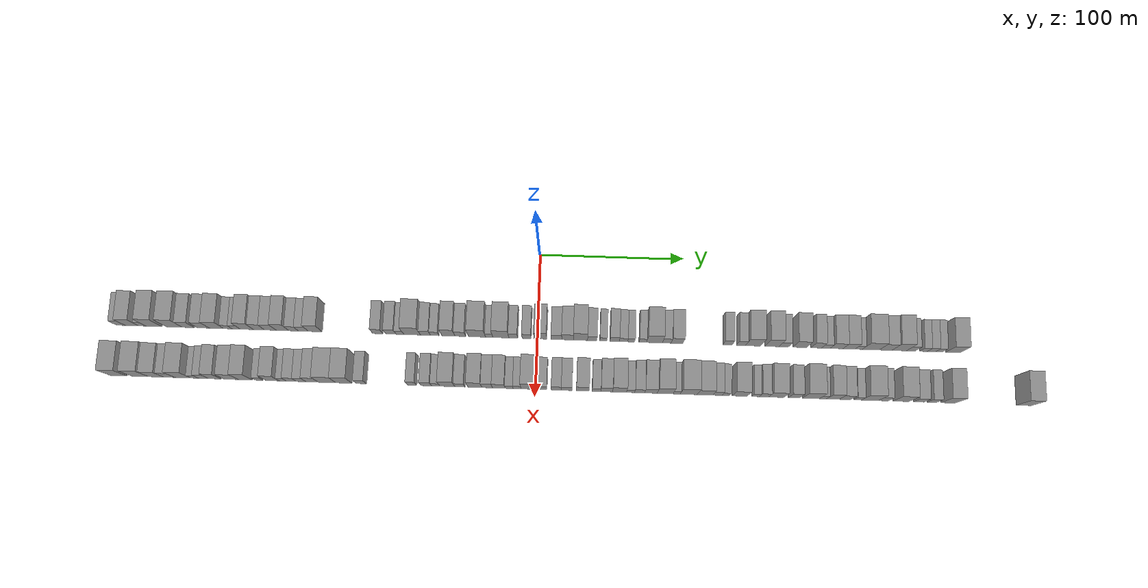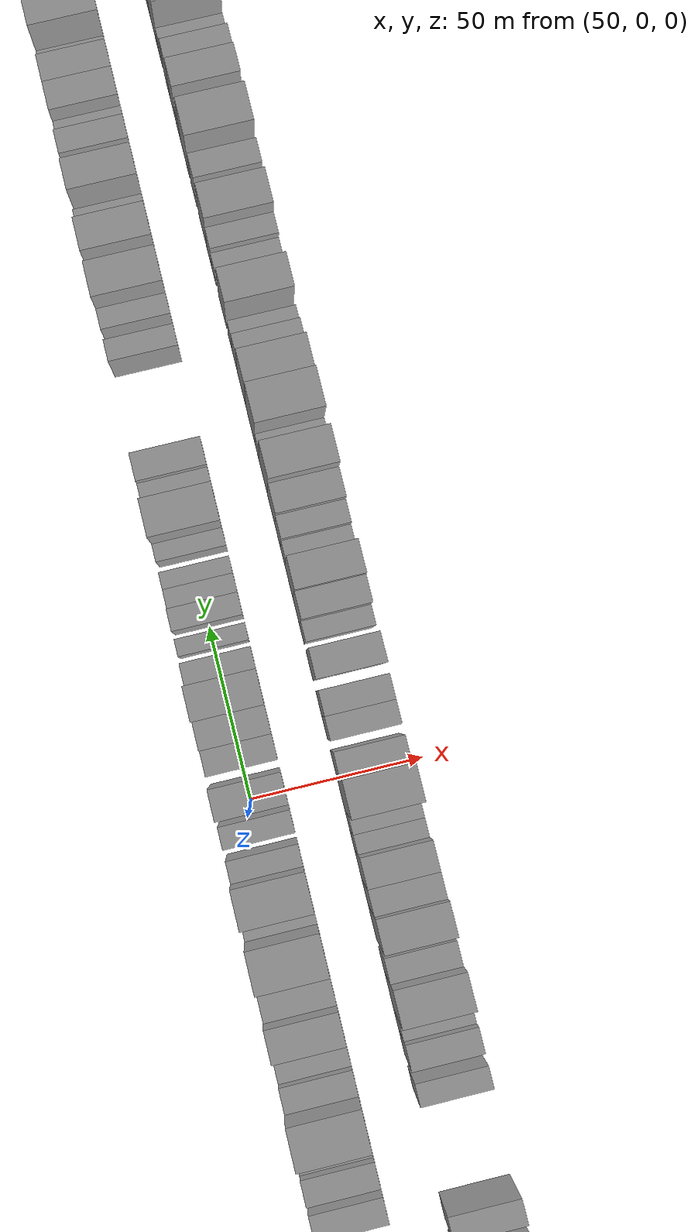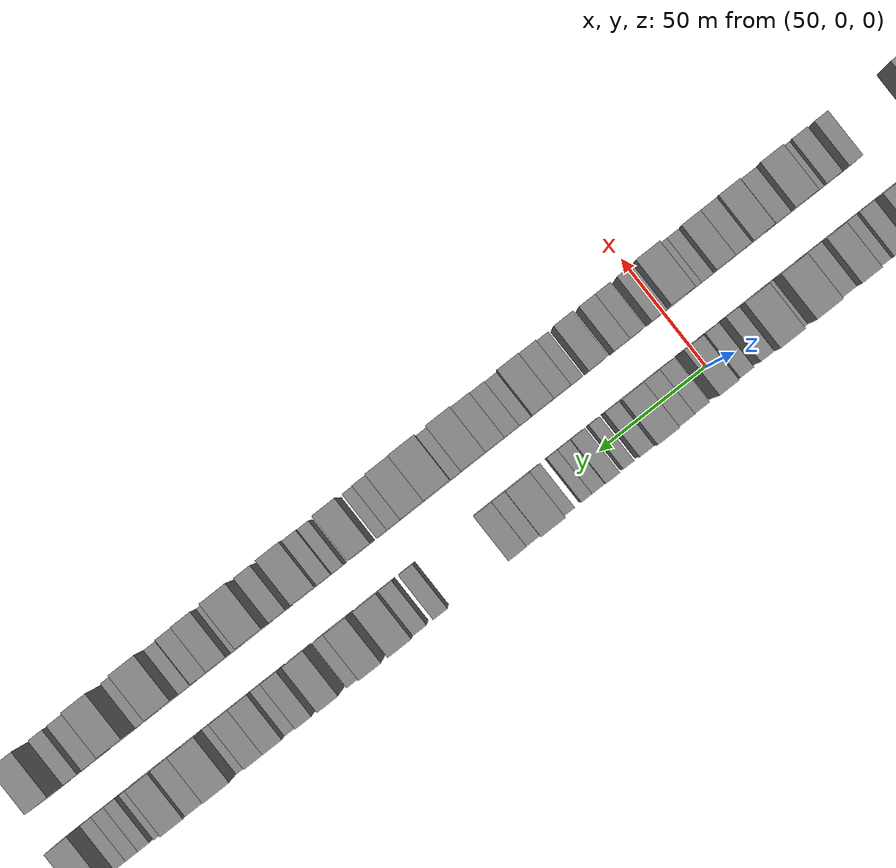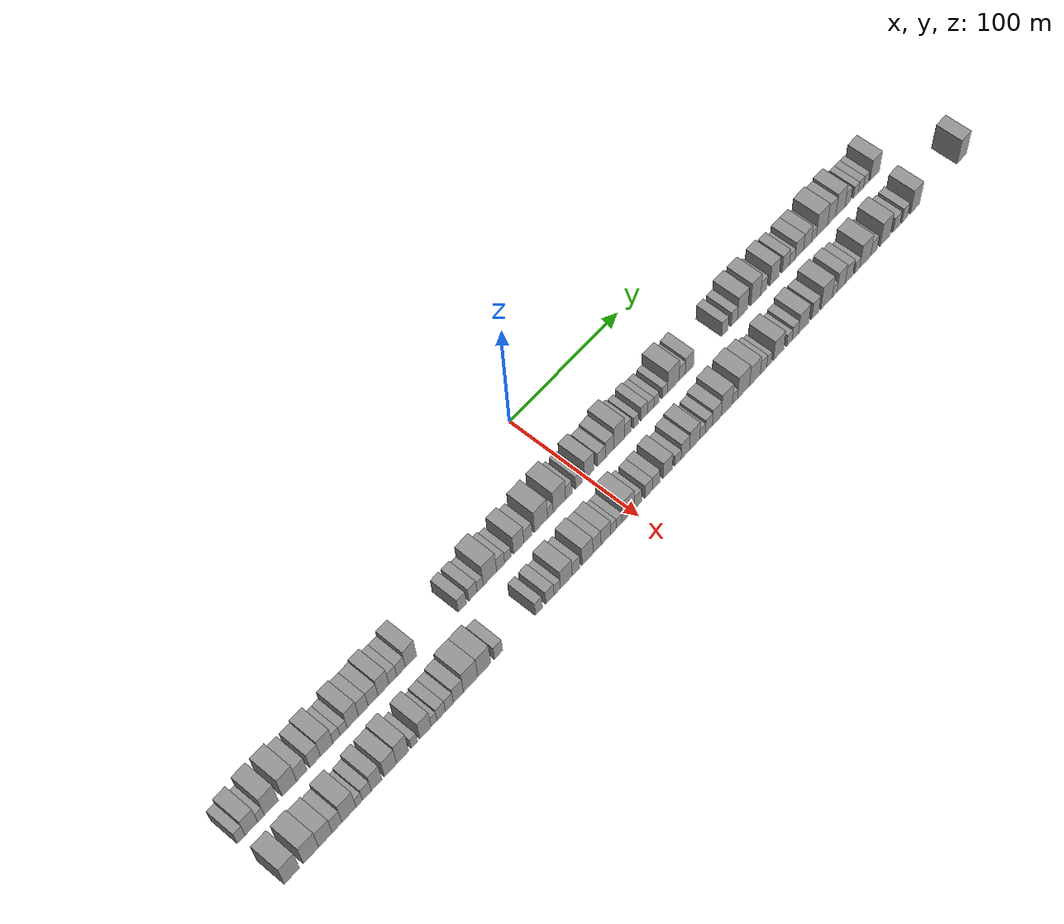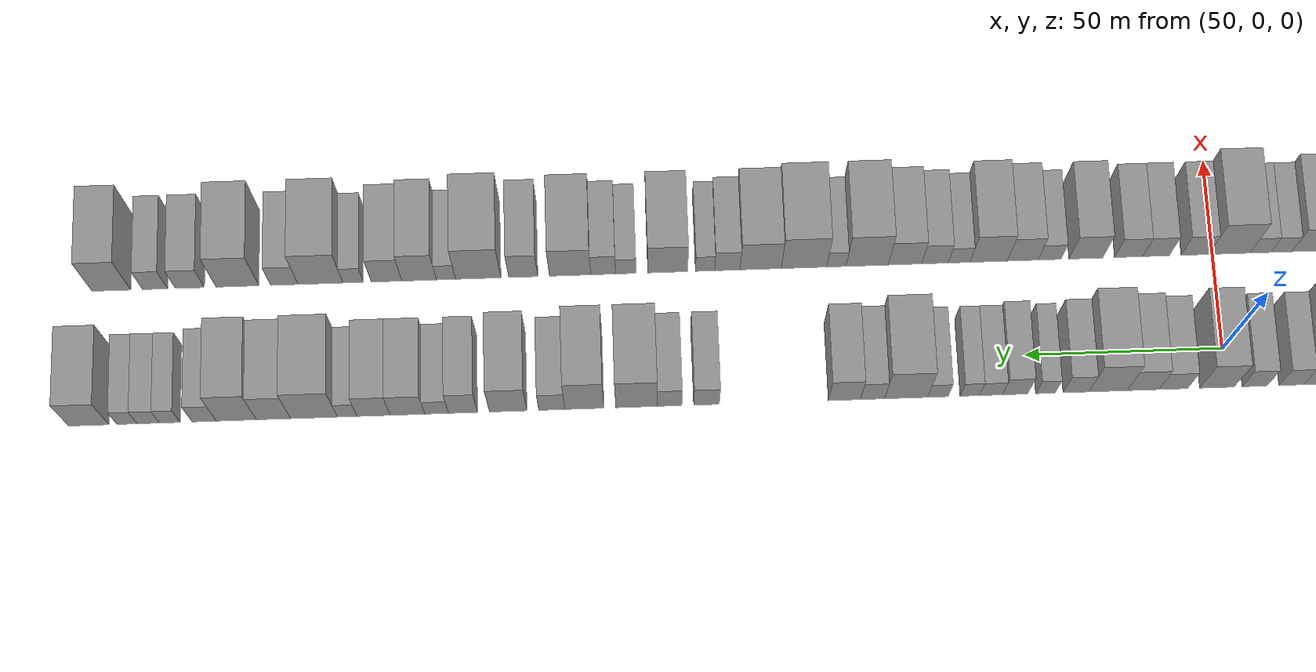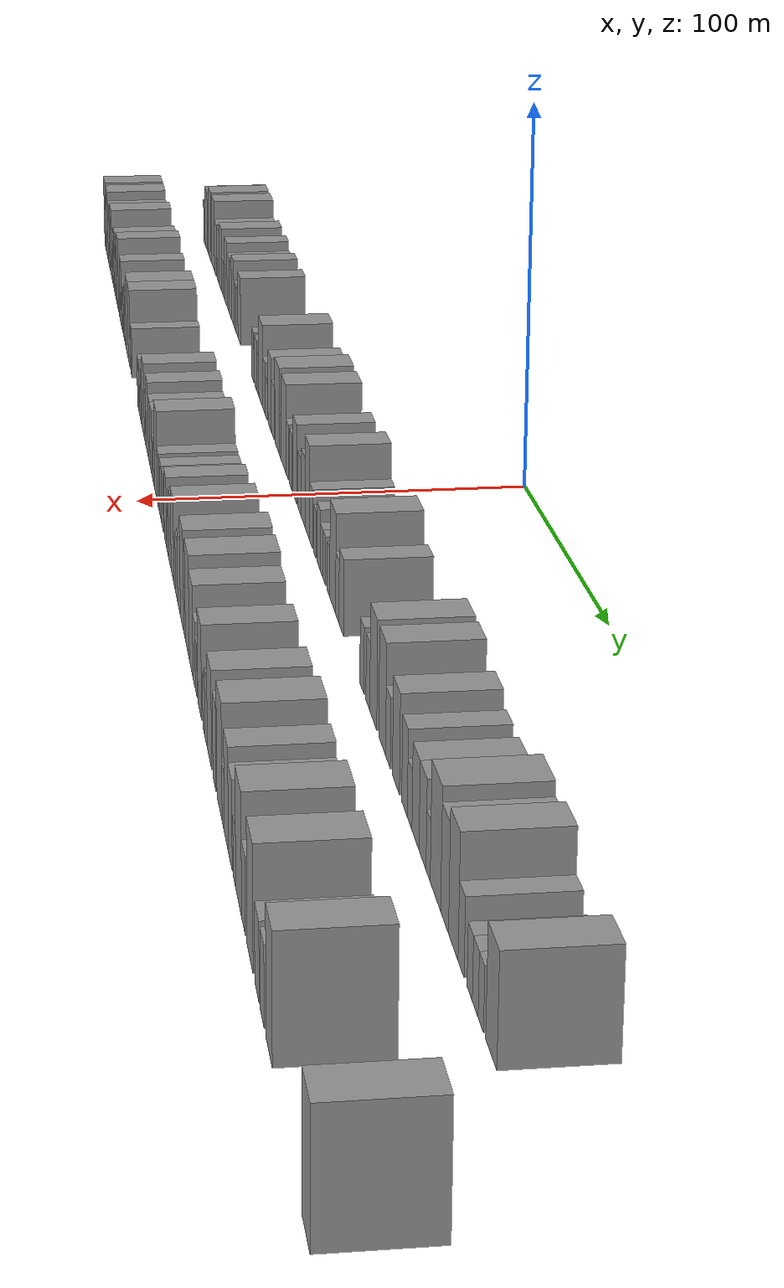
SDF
<sdf version="1.6">
 <world name="default">
  <scene>
   <sky><clouds><speed>12</speed></clouds></sky>
   <ambient>0.4 0.4 0.4 1</ambient>
   <background>0.7 0.7 0.7 1</background>
   <shadows>1</shadows>
  </scene>
  <gravity>0 0 -9.8066</gravity>
  <magnetic_field>6e-06 2.3e-05 -4.2e-05</magnetic_field>
  <physics default="0" name="default_physics" type="ode">
   <ode>
    <solver>
     <type>quick</type>
     <iters>10</iters>
     <sor>1.0</sor>
     <use_dynamic_moi_rescaling>0</use_dynamic_moi_rescaling>
    </solver>
    <constraints>
     <cfm>0</cfm>
     <erp>0.2</erp>
     <contact_max_correcting_vel>100</contact_max_correcting_vel>
     <contact_surface_layer>0.001</contact_surface_layer>
    </constraints>
   </ode>
   <max_step_size>0.004</max_step_size>
   <real_time_factor>1</real_time_factor>
   <real_time_update_rate>250</real_time_update_rate>
  </physics>
  <light name="sun" type="directional">
   <pose>0 0 10 0 0 0</pose>
   <diffuse>0.8 0.8 0.8 1</diffuse>
   <specular>0.2 0.2 0.2 1</specular>
   <attenuation>
    <range>1000</range>
    <constant>0.9</constant>
    <linear>0.01</linear>
    <quadratic>0.001</quadratic>
   </attenuation>
   <direction>-0.5 0.1 -0.9</direction>
  </light>
  <model name="building_1">
   <static>1</static>
   <pose>50.0000 -286.9700 0 0.000000 0.000000 0.000000</pose>
   <link name="link">
    <pose>0 0 7.50 0 0 0</pose>
    <collision name="collision"><geometry><box><size>20.0000 6.0599 15.0000</size></box></geometry></collision>
    <visual name="visual">
     <cast_shadows>0</cast_shadows>
     <geometry><box><size>20.0000 6.0599 15.0000</size></box></geometry>
     <material>
      <script>
       <uri>model://grey_wall/materials/scripts</uri>
       <uri>model://grey_wall/materials/textures</uri>
       <name>vrc/grey_wall</name>
      </script>
     </material>
    </visual>
   </link>
  </model>
  <model name="building_2">
   <static>1</static>
   <pose>50.0000 -279.1994 0 0.000000 0.000000 0.000000</pose>
   <link name="link">
    <pose>0 0 10.50 0 0 0</pose>
    <collision name="collision"><geometry><box><size>20.0000 9.4813 21.0000</size></box></geometry></collision>
    <visual name="visual">
     <cast_shadows>0</cast_shadows>
     <geometry><box><size>20.0000 9.4813 21.0000</size></box></geometry>
     <material>
      <script>
       <uri>model://grey_wall/materials/scripts</uri>
       <uri>model://grey_wall/materials/textures</uri>
       <name>vrc/grey_wall</name>
      </script>
     </material>
    </visual>
   </link>
  </model>
  <model name="building_3">
   <static>1</static>
   <pose>50.0000 -271.9404 0 0.000000 0.000000 0.000000</pose>
   <link name="link">
    <pose>0 0 6.00 0 0 0</pose>
    <collision name="collision"><geometry><box><size>20.0000 5.0366 12.0000</size></box></geometry></collision>
    <visual name="visual">
     <cast_shadows>0</cast_shadows>
     <geometry><box><size>20.0000 5.0366 12.0000</size></box></geometry>
     <material>
      <script>
       <uri>model://grey_wall/materials/scripts</uri>
       <uri>model://grey_wall/materials/textures</uri>
       <name>vrc/grey_wall</name>
      </script>
     </material>
    </visual>
   </link>
  </model>
  <model name="building_4">
   <static>1</static>
   <pose>50.0000 -263.9885 0 0.000000 0.000000 0.000000</pose>
   <link name="link">
    <pose>0 0 12.00 0 0 0</pose>
    <collision name="collision"><geometry><box><size>20.0000 10.8672 24.0000</size></box></geometry></collision>
    <visual name="visual">
     <cast_shadows>0</cast_shadows>
     <geometry><box><size>20.0000 10.8672 24.0000</size></box></geometry>
     <material>
      <script>
       <uri>model://grey_wall/materials/scripts</uri>
       <uri>model://grey_wall/materials/textures</uri>
       <name>vrc/grey_wall</name>
      </script>
     </material>
    </visual>
   </link>
  </model>
  <model name="building_5">
   <static>1</static>
   <pose>50.0000 -250.0232 0 0.000000 0.000000 0.000000</pose>
   <link name="link">
    <pose>0 0 12.00 0 0 0</pose>
    <collision name="collision"><geometry><box><size>20.0000 11.0633 24.0000</size></box></geometry></collision>
    <visual name="visual">
     <cast_shadows>0</cast_shadows>
     <geometry><box><size>20.0000 11.0633 24.0000</size></box></geometry>
     <material>
      <script>
       <uri>model://grey_wall/materials/scripts</uri>
       <uri>model://grey_wall/materials/textures</uri>
       <name>vrc/grey_wall</name>
      </script>
     </material>
    </visual>
   </link>
  </model>
  <model name="building_6">
   <static>1</static>
   <pose>50.0000 -240.3113 0 0.000000 0.000000 0.000000</pose>
   <link name="link">
    <pose>0 0 9.00 0 0 0</pose>
    <collision name="collision"><geometry><box><size>20.0000 8.3603 18.0000</size></box></geometry></collision>
    <visual name="visual">
     <cast_shadows>0</cast_shadows>
     <geometry><box><size>20.0000 8.3603 18.0000</size></box></geometry>
     <material>
      <script>
       <uri>model://grey_wall/materials/scripts</uri>
       <uri>model://grey_wall/materials/textures</uri>
       <name>vrc/grey_wall</name>
      </script>
     </material>
    </visual>
   </link>
  </model>
  <model name="building_7">
   <static>1</static>
   <pose>50.0000 -229.9773 0 0.000000 0.000000 0.000000</pose>
   <link name="link">
    <pose>0 0 9.00 0 0 0</pose>
    <collision name="collision"><geometry><box><size>20.0000 8.3078 18.0000</size></box></geometry></collision>
    <visual name="visual">
     <cast_shadows>0</cast_shadows>
     <geometry><box><size>20.0000 8.3078 18.0000</size></box></geometry>
     <material>
      <script>
       <uri>model://grey_wall/materials/scripts</uri>
       <uri>model://grey_wall/materials/textures</uri>
       <name>vrc/grey_wall</name>
      </script>
     </material>
    </visual>
   </link>
  </model>
  <model name="building_8">
   <static>1</static>
   <pose>50.0000 -220.8334 0 0.000000 0.000000 0.000000</pose>
   <link name="link">
    <pose>0 0 10.50 0 0 0</pose>
    <collision name="collision"><geometry><box><size>20.0000 9.9800 21.0000</size></box></geometry></collision>
    <visual name="visual">
     <cast_shadows>0</cast_shadows>
     <geometry><box><size>20.0000 9.9800 21.0000</size></box></geometry>
     <material>
      <script>
       <uri>model://grey_wall/materials/scripts</uri>
       <uri>model://grey_wall/materials/textures</uri>
       <name>vrc/grey_wall</name>
      </script>
     </material>
    </visual>
   </link>
  </model>
  <model name="building_9">
   <static>1</static>
   <pose>50.0000 -212.9741 0 0.000000 0.000000 0.000000</pose>
   <link name="link">
    <pose>0 0 6.00 0 0 0</pose>
    <collision name="collision"><geometry><box><size>20.0000 5.7386 12.0000</size></box></geometry></collision>
    <visual name="visual">
     <cast_shadows>0</cast_shadows>
     <geometry><box><size>20.0000 5.7386 12.0000</size></box></geometry>
     <material>
      <script>
       <uri>model://grey_wall/materials/scripts</uri>
       <uri>model://grey_wall/materials/textures</uri>
       <name>vrc/grey_wall</name>
      </script>
     </material>
    </visual>
   </link>
  </model>
  <model name="building_10">
   <static>1</static>
   <pose>50.0000 -207.2779 0 0.000000 0.000000 0.000000</pose>
   <link name="link">
    <pose>0 0 6.00 0 0 0</pose>
    <collision name="collision"><geometry><box><size>20.0000 5.6538 12.0000</size></box></geometry></collision>
    <visual name="visual">
     <cast_shadows>0</cast_shadows>
     <geometry><box><size>20.0000 5.6538 12.0000</size></box></geometry>
     <material>
      <script>
       <uri>model://grey_wall/materials/scripts</uri>
       <uri>model://grey_wall/materials/textures</uri>
       <name>vrc/grey_wall</name>
      </script>
     </material>
    </visual>
   </link>
  </model>
  <model name="building_11">
   <static>1</static>
   <pose>50.0000 -199.9034 0 0.000000 0.000000 0.000000</pose>
   <link name="link">
    <pose>0 0 10.50 0 0 0</pose>
    <collision name="collision"><geometry><box><size>20.0000 9.0951 21.0000</size></box></geometry></collision>
    <visual name="visual">
     <cast_shadows>0</cast_shadows>
     <geometry><box><size>20.0000 9.0951 21.0000</size></box></geometry>
     <material>
      <script>
       <uri>model://grey_wall/materials/scripts</uri>
       <uri>model://grey_wall/materials/textures</uri>
       <name>vrc/grey_wall</name>
      </script>
     </material>
    </visual>
   </link>
  </model>
  <model name="building_12">
   <static>1</static>
   <pose>50.0000 -191.4771 0 0.000000 0.000000 0.000000</pose>
   <link name="link">
    <pose>0 0 9.00 0 0 0</pose>
    <collision name="collision"><geometry><box><size>20.0000 7.7576 18.0000</size></box></geometry></collision>
    <visual name="visual">
     <cast_shadows>0</cast_shadows>
     <geometry><box><size>20.0000 7.7576 18.0000</size></box></geometry>
     <material>
      <script>
       <uri>model://grey_wall/materials/scripts</uri>
       <uri>model://grey_wall/materials/textures</uri>
       <name>vrc/grey_wall</name>
      </script>
     </material>
    </visual>
   </link>
  </model>
  <model name="building_13">
   <static>1</static>
   <pose>50.0000 -183.5973 0 0.000000 0.000000 0.000000</pose>
   <link name="link">
    <pose>0 0 9.00 0 0 0</pose>
    <collision name="collision"><geometry><box><size>20.0000 8.0020 18.0000</size></box></geometry></collision>
    <visual name="visual">
     <cast_shadows>0</cast_shadows>
     <geometry><box><size>20.0000 8.0020 18.0000</size></box></geometry>
     <material>
      <script>
       <uri>model://grey_wall/materials/scripts</uri>
       <uri>model://grey_wall/materials/textures</uri>
       <name>vrc/grey_wall</name>
      </script>
     </material>
    </visual>
   </link>
  </model>
  <model name="building_14">
   <static>1</static>
   <pose>50.0000 -175.2231 0 0.000000 0.000000 0.000000</pose>
   <link name="link">
    <pose>0 0 10.50 0 0 0</pose>
    <collision name="collision"><geometry><box><size>20.0000 8.7465 21.0000</size></box></geometry></collision>
    <visual name="visual">
     <cast_shadows>0</cast_shadows>
     <geometry><box><size>20.0000 8.7465 21.0000</size></box></geometry>
     <material>
      <script>
       <uri>model://grey_wall/materials/scripts</uri>
       <uri>model://grey_wall/materials/textures</uri>
       <name>vrc/grey_wall</name>
      </script>
     </material>
    </visual>
   </link>
  </model>
  <model name="building_15">
   <static>1</static>
   <pose>50.0000 -167.5827 0 0.000000 0.000000 0.000000</pose>
   <link name="link">
    <pose>0 0 7.50 0 0 0</pose>
    <collision name="collision"><geometry><box><size>20.0000 6.5344 15.0000</size></box></geometry></collision>
    <visual name="visual">
     <cast_shadows>0</cast_shadows>
     <geometry><box><size>20.0000 6.5344 15.0000</size></box></geometry>
     <material>
      <script>
       <uri>model://grey_wall/materials/scripts</uri>
       <uri>model://grey_wall/materials/textures</uri>
       <name>vrc/grey_wall</name>
      </script>
     </material>
    </visual>
   </link>
  </model>
  <model name="building_16">
   <static>1</static>
   <pose>50.0000 -160.8261 0 0.000000 0.000000 0.000000</pose>
   <link name="link">
    <pose>0 0 7.50 0 0 0</pose>
    <collision name="collision"><geometry><box><size>20.0000 6.9788 15.0000</size></box></geometry></collision>
    <visual name="visual">
     <cast_shadows>0</cast_shadows>
     <geometry><box><size>20.0000 6.9788 15.0000</size></box></geometry>
     <material>
      <script>
       <uri>model://grey_wall/materials/scripts</uri>
       <uri>model://grey_wall/materials/textures</uri>
       <name>vrc/grey_wall</name>
      </script>
     </material>
    </visual>
   </link>
  </model>
  <model name="building_17">
   <static>1</static>
   <pose>50.0000 -152.6693 0 0.000000 0.000000 0.000000</pose>
   <link name="link">
    <pose>0 0 10.50 0 0 0</pose>
    <collision name="collision"><geometry><box><size>20.0000 9.3348 21.0000</size></box></geometry></collision>
    <visual name="visual">
     <cast_shadows>0</cast_shadows>
     <geometry><box><size>20.0000 9.3348 21.0000</size></box></geometry>
     <material>
      <script>
       <uri>model://grey_wall/materials/scripts</uri>
       <uri>model://grey_wall/materials/textures</uri>
       <name>vrc/grey_wall</name>
      </script>
     </material>
    </visual>
   </link>
  </model>
  <model name="building_18">
   <static>1</static>
   <pose>50.0000 -109.4901 0 0.000000 0.000000 0.000000</pose>
   <link name="link">
    <pose>0 0 7.50 0 0 0</pose>
    <collision name="collision"><geometry><box><size>20.0000 7.0079 15.0000</size></box></geometry></collision>
    <visual name="visual">
     <cast_shadows>0</cast_shadows>
     <geometry><box><size>20.0000 7.0079 15.0000</size></box></geometry>
     <material>
      <script>
       <uri>model://grey_wall/materials/scripts</uri>
       <uri>model://grey_wall/materials/textures</uri>
       <name>vrc/grey_wall</name>
      </script>
     </material>
    </visual>
   </link>
  </model>
  <model name="building_19">
   <static>1</static>
   <pose>50.0000 -100.4679 0 0.000000 0.000000 0.000000</pose>
   <link name="link">
    <pose>0 0 7.50 0 0 0</pose>
    <collision name="collision"><geometry><box><size>20.0000 7.0365 15.0000</size></box></geometry></collision>
    <visual name="visual">
     <cast_shadows>0</cast_shadows>
     <geometry><box><size>20.0000 7.0365 15.0000</size></box></geometry>
     <material>
      <script>
       <uri>model://grey_wall/materials/scripts</uri>
       <uri>model://grey_wall/materials/textures</uri>
       <name>vrc/grey_wall</name>
      </script>
     </material>
    </visual>
   </link>
  </model>
  <model name="building_20">
   <static>1</static>
   <pose>50.0000 -94.2557 0 0.000000 0.000000 0.000000</pose>
   <link name="link">
    <pose>0 0 6.00 0 0 0</pose>
    <collision name="collision"><geometry><box><size>20.0000 5.3881 12.0000</size></box></geometry></collision>
    <visual name="visual">
     <cast_shadows>0</cast_shadows>
     <geometry><box><size>20.0000 5.3881 12.0000</size></box></geometry>
     <material>
      <script>
       <uri>model://grey_wall/materials/scripts</uri>
       <uri>model://grey_wall/materials/textures</uri>
       <name>vrc/grey_wall</name>
      </script>
     </material>
    </visual>
   </link>
  </model>
  <model name="building_21">
   <static>1</static>
   <pose>50.0000 -85.8278 0 0.000000 0.000000 0.000000</pose>
   <link name="link">
    <pose>0 0 12.00 0 0 0</pose>
    <collision name="collision"><geometry><box><size>20.0000 11.4677 24.0000</size></box></geometry></collision>
    <visual name="visual">
     <cast_shadows>0</cast_shadows>
     <geometry><box><size>20.0000 11.4677 24.0000</size></box></geometry>
     <material>
      <script>
       <uri>model://grey_wall/materials/scripts</uri>
       <uri>model://grey_wall/materials/textures</uri>
       <name>vrc/grey_wall</name>
      </script>
     </material>
    </visual>
   </link>
  </model>
  <model name="building_22">
   <static>1</static>
   <pose>50.0000 -76.6382 0 0.000000 0.000000 0.000000</pose>
   <link name="link">
    <pose>0 0 7.50 0 0 0</pose>
    <collision name="collision"><geometry><box><size>20.0000 6.9115 15.0000</size></box></geometry></collision>
    <visual name="visual">
     <cast_shadows>0</cast_shadows>
     <geometry><box><size>20.0000 6.9115 15.0000</size></box></geometry>
     <material>
      <script>
       <uri>model://grey_wall/materials/scripts</uri>
       <uri>model://grey_wall/materials/textures</uri>
       <name>vrc/grey_wall</name>
      </script>
     </material>
    </visual>
   </link>
  </model>
  <model name="building_23">
   <static>1</static>
   <pose>50.0000 -70.2696 0 0.000000 0.000000 0.000000</pose>
   <link name="link">
    <pose>0 0 6.00 0 0 0</pose>
    <collision name="collision"><geometry><box><size>20.0000 5.8257 12.0000</size></box></geometry></collision>
    <visual name="visual">
     <cast_shadows>0</cast_shadows>
     <geometry><box><size>20.0000 5.8257 12.0000</size></box></geometry>
     <material>
      <script>
       <uri>model://grey_wall/materials/scripts</uri>
       <uri>model://grey_wall/materials/textures</uri>
       <name>vrc/grey_wall</name>
      </script>
     </material>
    </visual>
   </link>
  </model>
  <model name="building_24">
   <static>1</static>
   <pose>50.0000 -60.8436 0 0.000000 0.000000 0.000000</pose>
   <link name="link">
    <pose>0 0 10.50 0 0 0</pose>
    <collision name="collision"><geometry><box><size>20.0000 9.0262 21.0000</size></box></geometry></collision>
    <visual name="visual">
     <cast_shadows>0</cast_shadows>
     <geometry><box><size>20.0000 9.0262 21.0000</size></box></geometry>
     <material>
      <script>
       <uri>model://grey_wall/materials/scripts</uri>
       <uri>model://grey_wall/materials/textures</uri>
       <name>vrc/grey_wall</name>
      </script>
     </material>
    </visual>
   </link>
  </model>
  <model name="building_25">
   <static>1</static>
   <pose>50.0000 -52.6606 0 0.000000 0.000000 0.000000</pose>
   <link name="link">
    <pose>0 0 7.50 0 0 0</pose>
    <collision name="collision"><geometry><box><size>20.0000 7.3399 15.0000</size></box></geometry></collision>
    <visual name="visual">
     <cast_shadows>0</cast_shadows>
     <geometry><box><size>20.0000 7.3399 15.0000</size></box></geometry>
     <material>
      <script>
       <uri>model://grey_wall/materials/scripts</uri>
       <uri>model://grey_wall/materials/textures</uri>
       <name>vrc/grey_wall</name>
      </script>
     </material>
    </visual>
   </link>
  </model>
  <model name="building_26">
   <static>1</static>
   <pose>50.0000 -41.1593 0 0.000000 0.000000 0.000000</pose>
   <link name="link">
    <pose>0 0 12.00 0 0 0</pose>
    <collision name="collision"><geometry><box><size>20.0000 11.6628 24.0000</size></box></geometry></collision>
    <visual name="visual">
     <cast_shadows>0</cast_shadows>
     <geometry><box><size>20.0000 11.6628 24.0000</size></box></geometry>
     <material>
      <script>
       <uri>model://grey_wall/materials/scripts</uri>
       <uri>model://grey_wall/materials/textures</uri>
       <name>vrc/grey_wall</name>
      </script>
     </material>
    </visual>
   </link>
  </model>
  <model name="building_27">
   <static>1</static>
   <pose>50.0000 -32.8306 0 0.000000 0.000000 0.000000</pose>
   <link name="link">
    <pose>0 0 6.00 0 0 0</pose>
    <collision name="collision"><geometry><box><size>20.0000 4.9946 12.0000</size></box></geometry></collision>
    <visual name="visual">
     <cast_shadows>0</cast_shadows>
     <geometry><box><size>20.0000 4.9946 12.0000</size></box></geometry>
     <material>
      <script>
       <uri>model://grey_wall/materials/scripts</uri>
       <uri>model://grey_wall/materials/textures</uri>
       <name>vrc/grey_wall</name>
      </script>
     </material>
    </visual>
   </link>
  </model>
  <model name="building_28">
   <static>1</static>
   <pose>50.0000 -24.8068 0 0.000000 0.000000 0.000000</pose>
   <link name="link">
    <pose>0 0 12.00 0 0 0</pose>
    <collision name="collision"><geometry><box><size>20.0000 11.0529 24.0000</size></box></geometry></collision>
    <visual name="visual">
     <cast_shadows>0</cast_shadows>
     <geometry><box><size>20.0000 11.0529 24.0000</size></box></geometry>
     <material>
      <script>
       <uri>model://grey_wall/materials/scripts</uri>
       <uri>model://grey_wall/materials/textures</uri>
       <name>vrc/grey_wall</name>
      </script>
     </material>
    </visual>
   </link>
  </model>
  <model name="building_29">
   <static>1</static>
   <pose>50.0000 -16.2372 0 0.000000 0.000000 0.000000</pose>
   <link name="link">
    <pose>0 0 7.50 0 0 0</pose>
    <collision name="collision"><geometry><box><size>20.0000 6.0862 15.0000</size></box></geometry></collision>
    <visual name="visual">
     <cast_shadows>0</cast_shadows>
     <geometry><box><size>20.0000 6.0862 15.0000</size></box></geometry>
     <material>
      <script>
       <uri>model://grey_wall/materials/scripts</uri>
       <uri>model://grey_wall/materials/textures</uri>
       <name>vrc/grey_wall</name>
      </script>
     </material>
    </visual>
   </link>
  </model>
  <model name="building_30">
   <static>1</static>
   <pose>50.0000 -7.0716 0 0.000000 0.000000 0.000000</pose>
   <link name="link">
    <pose>0 0 7.50 0 0 0</pose>
    <collision name="collision"><geometry><box><size>20.0000 6.2450 15.0000</size></box></geometry></collision>
    <visual name="visual">
     <cast_shadows>0</cast_shadows>
     <geometry><box><size>20.0000 6.2450 15.0000</size></box></geometry>
     <material>
      <script>
       <uri>model://grey_wall/materials/scripts</uri>
       <uri>model://grey_wall/materials/textures</uri>
       <name>vrc/grey_wall</name>
      </script>
     </material>
    </visual>
   </link>
  </model>
  <model name="building_31">
   <static>1</static>
   <pose>50.0000 2.4005 0 0.000000 0.000000 0.000000</pose>
   <link name="link">
    <pose>0 0 10.50 0 0 0</pose>
    <collision name="collision"><geometry><box><size>20.0000 8.6992 21.0000</size></box></geometry></collision>
    <visual name="visual">
     <cast_shadows>0</cast_shadows>
     <geometry><box><size>20.0000 8.6992 21.0000</size></box></geometry>
     <material>
      <script>
       <uri>model://grey_wall/materials/scripts</uri>
       <uri>model://grey_wall/materials/textures</uri>
       <name>vrc/grey_wall</name>
      </script>
     </material>
    </visual>
   </link>
  </model>
  <model name="building_32">
   <static>1</static>
   <pose>50.0000 13.3636 0 0.000000 0.000000 0.000000</pose>
   <link name="link">
    <pose>0 0 7.50 0 0 0</pose>
    <collision name="collision"><geometry><box><size>20.0000 7.2272 15.0000</size></box></geometry></collision>
    <visual name="visual">
     <cast_shadows>0</cast_shadows>
     <geometry><box><size>20.0000 7.2272 15.0000</size></box></geometry>
     <material>
      <script>
       <uri>model://grey_wall/materials/scripts</uri>
       <uri>model://grey_wall/materials/textures</uri>
       <name>vrc/grey_wall</name>
      </script>
     </material>
    </visual>
   </link>
  </model>
  <model name="building_33">
   <static>1</static>
   <pose>50.0000 20.9551 0 0.000000 0.000000 0.000000</pose>
   <link name="link">
    <pose>0 0 9.00 0 0 0</pose>
    <collision name="collision"><geometry><box><size>20.0000 7.9557 18.0000</size></box></geometry></collision>
    <visual name="visual">
     <cast_shadows>0</cast_shadows>
     <geometry><box><size>20.0000 7.9557 18.0000</size></box></geometry>
     <material>
      <script>
       <uri>model://grey_wall/materials/scripts</uri>
       <uri>model://grey_wall/materials/textures</uri>
       <name>vrc/grey_wall</name>
      </script>
     </material>
    </visual>
   </link>
  </model>
  <model name="building_34">
   <static>1</static>
   <pose>50.0000 29.8034 0 0.000000 0.000000 0.000000</pose>
   <link name="link">
    <pose>0 0 12.00 0 0 0</pose>
    <collision name="collision"><geometry><box><size>20.0000 9.7410 24.0000</size></box></geometry></collision>
    <visual name="visual">
     <cast_shadows>0</cast_shadows>
     <geometry><box><size>20.0000 9.7410 24.0000</size></box></geometry>
     <material>
      <script>
       <uri>model://grey_wall/materials/scripts</uri>
       <uri>model://grey_wall/materials/textures</uri>
       <name>vrc/grey_wall</name>
      </script>
     </material>
    </visual>
   </link>
  </model>
  <model name="building_35">
   <static>1</static>
   <pose>50.0000 37.9093 0 0.000000 0.000000 0.000000</pose>
   <link name="link">
    <pose>0 0 7.50 0 0 0</pose>
    <collision name="collision"><geometry><box><size>20.0000 6.4709 15.0000</size></box></geometry></collision>
    <visual name="visual">
     <cast_shadows>0</cast_shadows>
     <geometry><box><size>20.0000 6.4709 15.0000</size></box></geometry>
     <material>
      <script>
       <uri>model://grey_wall/materials/scripts</uri>
       <uri>model://grey_wall/materials/textures</uri>
       <name>vrc/grey_wall</name>
      </script>
     </material>
    </visual>
   </link>
  </model>
  <model name="building_36">
   <static>1</static>
   <pose>50.0000 45.5995 0 0.000000 0.000000 0.000000</pose>
   <link name="link">
    <pose>0 0 6.00 0 0 0</pose>
    <collision name="collision"><geometry><box><size>20.0000 4.9094 12.0000</size></box></geometry></collision>
    <visual name="visual">
     <cast_shadows>0</cast_shadows>
     <geometry><box><size>20.0000 4.9094 12.0000</size></box></geometry>
     <material>
      <script>
       <uri>model://grey_wall/materials/scripts</uri>
       <uri>model://grey_wall/materials/textures</uri>
       <name>vrc/grey_wall</name>
      </script>
     </material>
    </visual>
   </link>
  </model>
  <model name="building_37">
   <static>1</static>
   <pose>50.0000 53.2452 0 0.000000 0.000000 0.000000</pose>
   <link name="link">
    <pose>0 0 7.50 0 0 0</pose>
    <collision name="collision"><geometry><box><size>20.0000 6.3820 15.0000</size></box></geometry></collision>
    <visual name="visual">
     <cast_shadows>0</cast_shadows>
     <geometry><box><size>20.0000 6.3820 15.0000</size></box></geometry>
     <material>
      <script>
       <uri>model://grey_wall/materials/scripts</uri>
       <uri>model://grey_wall/materials/textures</uri>
       <name>vrc/grey_wall</name>
      </script>
     </material>
    </visual>
   </link>
  </model>
  <model name="building_38">
   <static>1</static>
   <pose>50.0000 59.3104 0 0.000000 0.000000 0.000000</pose>
   <link name="link">
    <pose>0 0 6.00 0 0 0</pose>
    <collision name="collision"><geometry><box><size>20.0000 5.7483 12.0000</size></box></geometry></collision>
    <visual name="visual">
     <cast_shadows>0</cast_shadows>
     <geometry><box><size>20.0000 5.7483 12.0000</size></box></geometry>
     <material>
      <script>
       <uri>model://grey_wall/materials/scripts</uri>
       <uri>model://grey_wall/materials/textures</uri>
       <name>vrc/grey_wall</name>
      </script>
     </material>
    </visual>
   </link>
  </model>
  <model name="building_39">
   <static>1</static>
   <pose>50.0000 64.6195 0 0.000000 0.000000 0.000000</pose>
   <link name="link">
    <pose>0 0 6.00 0 0 0</pose>
    <collision name="collision"><geometry><box><size>20.0000 4.8699 12.0000</size></box></geometry></collision>
    <visual name="visual">
     <cast_shadows>0</cast_shadows>
     <geometry><box><size>20.0000 4.8699 12.0000</size></box></geometry>
     <material>
      <script>
       <uri>model://grey_wall/materials/scripts</uri>
       <uri>model://grey_wall/materials/textures</uri>
       <name>vrc/grey_wall</name>
      </script>
     </material>
    </visual>
   </link>
  </model>
  <model name="building_40">
   <static>1</static>
   <pose>50.0000 72.6378 0 0.000000 0.000000 0.000000</pose>
   <link name="link">
    <pose>0 0 6.00 0 0 0</pose>
    <collision name="collision"><geometry><box><size>20.0000 5.1669 12.0000</size></box></geometry></collision>
    <visual name="visual">
     <cast_shadows>0</cast_shadows>
     <geometry><box><size>20.0000 5.1669 12.0000</size></box></geometry>
     <material>
      <script>
       <uri>model://grey_wall/materials/scripts</uri>
       <uri>model://grey_wall/materials/textures</uri>
       <name>vrc/grey_wall</name>
      </script>
     </material>
    </visual>
   </link>
  </model>
  <model name="building_41">
   <static>1</static>
   <pose>50.0000 80.6413 0 0.000000 0.000000 0.000000</pose>
   <link name="link">
    <pose>0 0 12.00 0 0 0</pose>
    <collision name="collision"><geometry><box><size>20.0000 10.8400 24.0000</size></box></geometry></collision>
    <visual name="visual">
     <cast_shadows>0</cast_shadows>
     <geometry><box><size>20.0000 10.8400 24.0000</size></box></geometry>
     <material>
      <script>
       <uri>model://grey_wall/materials/scripts</uri>
       <uri>model://grey_wall/materials/textures</uri>
       <name>vrc/grey_wall</name>
      </script>
     </material>
    </visual>
   </link>
  </model>
  <model name="building_42">
   <static>1</static>
   <pose>50.0000 89.0804 0 0.000000 0.000000 0.000000</pose>
   <link name="link">
    <pose>0 0 7.50 0 0 0</pose>
    <collision name="collision"><geometry><box><size>20.0000 6.0383 15.0000</size></box></geometry></collision>
    <visual name="visual">
     <cast_shadows>0</cast_shadows>
     <geometry><box><size>20.0000 6.0383 15.0000</size></box></geometry>
     <material>
      <script>
       <uri>model://grey_wall/materials/scripts</uri>
       <uri>model://grey_wall/materials/textures</uri>
       <name>vrc/grey_wall</name>
      </script>
     </material>
    </visual>
   </link>
  </model>
  <model name="building_43">
   <static>1</static>
   <pose>50.0000 96.1338 0 0.000000 0.000000 0.000000</pose>
   <link name="link">
    <pose>0 0 9.00 0 0 0</pose>
    <collision name="collision"><geometry><box><size>20.0000 8.0684 18.0000</size></box></geometry></collision>
    <visual name="visual">
     <cast_shadows>0</cast_shadows>
     <geometry><box><size>20.0000 8.0684 18.0000</size></box></geometry>
     <material>
      <script>
       <uri>model://grey_wall/materials/scripts</uri>
       <uri>model://grey_wall/materials/textures</uri>
       <name>vrc/grey_wall</name>
      </script>
     </material>
    </visual>
   </link>
  </model>
  <model name="building_44">
   <static>1</static>
   <pose>50.0000 130.7554 0 0.000000 0.000000 0.000000</pose>
   <link name="link">
    <pose>0 0 7.50 0 0 0</pose>
    <collision name="collision"><geometry><box><size>20.0000 6.3916 15.0000</size></box></geometry></collision>
    <visual name="visual">
     <cast_shadows>0</cast_shadows>
     <geometry><box><size>20.0000 6.3916 15.0000</size></box></geometry>
     <material>
      <script>
       <uri>model://grey_wall/materials/scripts</uri>
       <uri>model://grey_wall/materials/textures</uri>
       <name>vrc/grey_wall</name>
      </script>
     </material>
    </visual>
   </link>
  </model>
  <model name="building_45">
   <static>1</static>
   <pose>50.0000 140.0205 0 0.000000 0.000000 0.000000</pose>
   <link name="link">
    <pose>0 0 7.50 0 0 0</pose>
    <collision name="collision"><geometry><box><size>20.0000 6.1386 15.0000</size></box></geometry></collision>
    <visual name="visual">
     <cast_shadows>0</cast_shadows>
     <geometry><box><size>20.0000 6.1386 15.0000</size></box></geometry>
     <material>
      <script>
       <uri>model://grey_wall/materials/scripts</uri>
       <uri>model://grey_wall/materials/textures</uri>
       <name>vrc/grey_wall</name>
      </script>
     </material>
    </visual>
   </link>
  </model>
  <model name="building_46">
   <static>1</static>
   <pose>50.0000 148.2780 0 0.000000 0.000000 0.000000</pose>
   <link name="link">
    <pose>0 0 12.00 0 0 0</pose>
    <collision name="collision"><geometry><box><size>20.0000 10.3763 24.0000</size></box></geometry></collision>
    <visual name="visual">
     <cast_shadows>0</cast_shadows>
     <geometry><box><size>20.0000 10.3763 24.0000</size></box></geometry>
     <material>
      <script>
       <uri>model://grey_wall/materials/scripts</uri>
       <uri>model://grey_wall/materials/textures</uri>
       <name>vrc/grey_wall</name>
      </script>
     </material>
    </visual>
   </link>
  </model>
  <model name="building_47">
   <static>1</static>
   <pose>50.0000 161.3583 0 0.000000 0.000000 0.000000</pose>
   <link name="link">
    <pose>0 0 12.00 0 0 0</pose>
    <collision name="collision"><geometry><box><size>20.0000 9.7842 24.0000</size></box></geometry></collision>
    <visual name="visual">
     <cast_shadows>0</cast_shadows>
     <geometry><box><size>20.0000 9.7842 24.0000</size></box></geometry>
     <material>
      <script>
       <uri>model://grey_wall/materials/scripts</uri>
       <uri>model://grey_wall/materials/textures</uri>
       <name>vrc/grey_wall</name>
      </script>
     </material>
    </visual>
   </link>
  </model>
  <model name="building_48">
   <static>1</static>
   <pose>50.0000 169.5037 0 0.000000 0.000000 0.000000</pose>
   <link name="link">
    <pose>0 0 7.50 0 0 0</pose>
    <collision name="collision"><geometry><box><size>20.0000 6.5066 15.0000</size></box></geometry></collision>
    <visual name="visual">
     <cast_shadows>0</cast_shadows>
     <geometry><box><size>20.0000 6.5066 15.0000</size></box></geometry>
     <material>
      <script>
       <uri>model://grey_wall/materials/scripts</uri>
       <uri>model://grey_wall/materials/textures</uri>
       <name>vrc/grey_wall</name>
      </script>
     </material>
    </visual>
   </link>
  </model>
  <model name="building_49">
   <static>1</static>
   <pose>50.0000 180.4436 0 0.000000 0.000000 0.000000</pose>
   <link name="link">
    <pose>0 0 10.50 0 0 0</pose>
    <collision name="collision"><geometry><box><size>20.0000 9.3733 21.0000</size></box></geometry></collision>
    <visual name="visual">
     <cast_shadows>0</cast_shadows>
     <geometry><box><size>20.0000 9.3733 21.0000</size></box></geometry>
     <material>
      <script>
       <uri>model://grey_wall/materials/scripts</uri>
       <uri>model://grey_wall/materials/textures</uri>
       <name>vrc/grey_wall</name>
      </script>
     </material>
    </visual>
   </link>
  </model>
  <model name="building_50">
   <static>1</static>
   <pose>50.0000 191.7479 0 0.000000 0.000000 0.000000</pose>
   <link name="link">
    <pose>0 0 9.00 0 0 0</pose>
    <collision name="collision"><geometry><box><size>20.0000 7.2354 18.0000</size></box></geometry></collision>
    <visual name="visual">
     <cast_shadows>0</cast_shadows>
     <geometry><box><size>20.0000 7.2354 18.0000</size></box></geometry>
     <material>
      <script>
       <uri>model://grey_wall/materials/scripts</uri>
       <uri>model://grey_wall/materials/textures</uri>
       <name>vrc/grey_wall</name>
      </script>
     </material>
    </visual>
   </link>
  </model>
  <model name="building_51">
   <static>1</static>
   <pose>50.0000 198.3375 0 0.000000 0.000000 0.000000</pose>
   <link name="link">
    <pose>0 0 6.00 0 0 0</pose>
    <collision name="collision"><geometry><box><size>20.0000 5.9438 12.0000</size></box></geometry></collision>
    <visual name="visual">
     <cast_shadows>0</cast_shadows>
     <geometry><box><size>20.0000 5.9438 12.0000</size></box></geometry>
     <material>
      <script>
       <uri>model://grey_wall/materials/scripts</uri>
       <uri>model://grey_wall/materials/textures</uri>
       <name>vrc/grey_wall</name>
      </script>
     </material>
    </visual>
   </link>
  </model>
  <model name="building_52">
   <static>1</static>
   <pose>50.0000 205.6407 0 0.000000 0.000000 0.000000</pose>
   <link name="link">
    <pose>0 0 9.00 0 0 0</pose>
    <collision name="collision"><geometry><box><size>20.0000 8.6625 18.0000</size></box></geometry></collision>
    <visual name="visual">
     <cast_shadows>0</cast_shadows>
     <geometry><box><size>20.0000 8.6625 18.0000</size></box></geometry>
     <material>
      <script>
       <uri>model://grey_wall/materials/scripts</uri>
       <uri>model://grey_wall/materials/textures</uri>
       <name>vrc/grey_wall</name>
      </script>
     </material>
    </visual>
   </link>
  </model>
  <model name="building_53">
   <static>1</static>
   <pose>50.0000 214.1257 0 0.000000 0.000000 0.000000</pose>
   <link name="link">
    <pose>0 0 9.00 0 0 0</pose>
    <collision name="collision"><geometry><box><size>20.0000 8.3075 18.0000</size></box></geometry></collision>
    <visual name="visual">
     <cast_shadows>0</cast_shadows>
     <geometry><box><size>20.0000 8.3075 18.0000</size></box></geometry>
     <material>
      <script>
       <uri>model://grey_wall/materials/scripts</uri>
       <uri>model://grey_wall/materials/textures</uri>
       <name>vrc/grey_wall</name>
      </script>
     </material>
    </visual>
   </link>
  </model>
  <model name="building_54">
   <static>1</static>
   <pose>50.0000 220.7303 0 0.000000 0.000000 0.000000</pose>
   <link name="link">
    <pose>0 0 6.00 0 0 0</pose>
    <collision name="collision"><geometry><box><size>20.0000 4.9018 12.0000</size></box></geometry></collision>
    <visual name="visual">
     <cast_shadows>0</cast_shadows>
     <geometry><box><size>20.0000 4.9018 12.0000</size></box></geometry>
     <material>
      <script>
       <uri>model://grey_wall/materials/scripts</uri>
       <uri>model://grey_wall/materials/textures</uri>
       <name>vrc/grey_wall</name>
      </script>
     </material>
    </visual>
   </link>
  </model>
  <model name="building_55">
   <static>1</static>
   <pose>50.0000 229.0439 0 0.000000 0.000000 0.000000</pose>
   <link name="link">
    <pose>0 0 12.00 0 0 0</pose>
    <collision name="collision"><geometry><box><size>20.0000 11.7254 24.0000</size></box></geometry></collision>
    <visual name="visual">
     <cast_shadows>0</cast_shadows>
     <geometry><box><size>20.0000 11.7254 24.0000</size></box></geometry>
     <material>
      <script>
       <uri>model://grey_wall/materials/scripts</uri>
       <uri>model://grey_wall/materials/textures</uri>
       <name>vrc/grey_wall</name>
      </script>
     </material>
    </visual>
   </link>
  </model>
  <model name="building_56">
   <static>1</static>
   <pose>50.0000 239.1916 0 0.000000 0.000000 0.000000</pose>
   <link name="link">
    <pose>0 0 10.50 0 0 0</pose>
    <collision name="collision"><geometry><box><size>20.0000 8.5701 21.0000</size></box></geometry></collision>
    <visual name="visual">
     <cast_shadows>0</cast_shadows>
     <geometry><box><size>20.0000 8.5701 21.0000</size></box></geometry>
     <material>
      <script>
       <uri>model://grey_wall/materials/scripts</uri>
       <uri>model://grey_wall/materials/textures</uri>
       <name>vrc/grey_wall</name>
      </script>
     </material>
    </visual>
   </link>
  </model>
  <model name="building_57">
   <static>1</static>
   <pose>50.0000 248.4637 0 0.000000 0.000000 0.000000</pose>
   <link name="link">
    <pose>0 0 12.00 0 0 0</pose>
    <collision name="collision"><geometry><box><size>20.0000 9.9740 24.0000</size></box></geometry></collision>
    <visual name="visual">
     <cast_shadows>0</cast_shadows>
     <geometry><box><size>20.0000 9.9740 24.0000</size></box></geometry>
     <material>
      <script>
       <uri>model://grey_wall/materials/scripts</uri>
       <uri>model://grey_wall/materials/textures</uri>
       <name>vrc/grey_wall</name>
      </script>
     </material>
    </visual>
   </link>
  </model>
  <model name="building_58">
   <static>1</static>
   <pose>50.0000 256.4814 0 0.000000 0.000000 0.000000</pose>
   <link name="link">
    <pose>0 0 7.50 0 0 0</pose>
    <collision name="collision"><geometry><box><size>20.0000 6.0614 15.0000</size></box></geometry></collision>
    <visual name="visual">
     <cast_shadows>0</cast_shadows>
     <geometry><box><size>20.0000 6.0614 15.0000</size></box></geometry>
     <material>
      <script>
       <uri>model://grey_wall/materials/scripts</uri>
       <uri>model://grey_wall/materials/textures</uri>
       <name>vrc/grey_wall</name>
      </script>
     </material>
    </visual>
   </link>
  </model>
  <model name="building_59">
   <static>1</static>
   <pose>50.0000 265.0682 0 0.000000 0.000000 0.000000</pose>
   <link name="link">
    <pose>0 0 6.00 0 0 0</pose>
    <collision name="collision"><geometry><box><size>20.0000 5.1121 12.0000</size></box></geometry></collision>
    <visual name="visual">
     <cast_shadows>0</cast_shadows>
     <geometry><box><size>20.0000 5.1121 12.0000</size></box></geometry>
     <material>
      <script>
       <uri>model://grey_wall/materials/scripts</uri>
       <uri>model://grey_wall/materials/textures</uri>
       <name>vrc/grey_wall</name>
      </script>
     </material>
    </visual>
   </link>
  </model>
  <model name="building_60">
   <static>1</static>
   <pose>50.0000 270.4138 0 0.000000 0.000000 0.000000</pose>
   <link name="link">
    <pose>0 0 6.00 0 0 0</pose>
    <collision name="collision"><geometry><box><size>20.0000 5.5793 12.0000</size></box></geometry></collision>
    <visual name="visual">
     <cast_shadows>0</cast_shadows>
     <geometry><box><size>20.0000 5.5793 12.0000</size></box></geometry>
     <material>
      <script>
       <uri>model://grey_wall/materials/scripts</uri>
       <uri>model://grey_wall/materials/textures</uri>
       <name>vrc/grey_wall</name>
      </script>
     </material>
    </visual>
   </link>
  </model>
  <model name="building_61">
   <static>1</static>
   <pose>50.0000 275.7355 0 0.000000 0.000000 0.000000</pose>
   <link name="link">
    <pose>0 0 6.00 0 0 0</pose>
    <collision name="collision"><geometry><box><size>20.0000 5.0640 12.0000</size></box></geometry></collision>
    <visual name="visual">
     <cast_shadows>0</cast_shadows>
     <geometry><box><size>20.0000 5.0640 12.0000</size></box></geometry>
     <material>
      <script>
       <uri>model://grey_wall/materials/scripts</uri>
       <uri>model://grey_wall/materials/textures</uri>
       <name>vrc/grey_wall</name>
      </script>
     </material>
    </visual>
   </link>
  </model>
  <model name="building_62">
   <static>1</static>
   <pose>50.0000 285.2897 0 0.000000 0.000000 0.000000</pose>
   <link name="link">
    <pose>0 0 10.50 0 0 0</pose>
    <collision name="collision"><geometry><box><size>20.0000 10.0445 21.0000</size></box></geometry></collision>
    <visual name="visual">
     <cast_shadows>0</cast_shadows>
     <geometry><box><size>20.0000 10.0445 21.0000</size></box></geometry>
     <material>
      <script>
       <uri>model://grey_wall/materials/scripts</uri>
       <uri>model://grey_wall/materials/textures</uri>
       <name>vrc/grey_wall</name>
      </script>
     </material>
    </visual>
   </link>
  </model>
  <model name="building_63">
   <static>1</static>
   <pose>85.0000 -284.2010 0 0.000000 0.000000 0.000000</pose>
   <link name="link">
    <pose>0 0 12.00 0 0 0</pose>
    <collision name="collision"><geometry><box><size>20.0000 11.5980 24.0000</size></box></geometry></collision>
    <visual name="visual">
     <cast_shadows>0</cast_shadows>
     <geometry><box><size>20.0000 11.5980 24.0000</size></box></geometry>
     <material>
      <script>
       <uri>model://grey_wall/materials/scripts</uri>
       <uri>model://grey_wall/materials/textures</uri>
       <name>vrc/grey_wall</name>
      </script>
     </material>
    </visual>
   </link>
  </model>
  <model name="building_64">
   <static>1</static>
   <pose>85.0000 -269.5314 0 0.000000 0.000000 0.000000</pose>
   <link name="link">
    <pose>0 0 12.00 0 0 0</pose>
    <collision name="collision"><geometry><box><size>20.0000 11.7412 24.0000</size></box></geometry></collision>
    <visual name="visual">
     <cast_shadows>0</cast_shadows>
     <geometry><box><size>20.0000 11.7412 24.0000</size></box></geometry>
     <material>
      <script>
       <uri>model://grey_wall/materials/scripts</uri>
       <uri>model://grey_wall/materials/textures</uri>
       <name>vrc/grey_wall</name>
      </script>
     </material>
    </visual>
   </link>
  </model>
  <model name="building_65">
   <static>1</static>
   <pose>85.0000 -258.4380 0 0.000000 0.000000 0.000000</pose>
   <link name="link">
    <pose>0 0 10.50 0 0 0</pose>
    <collision name="collision"><geometry><box><size>20.0000 10.4457 21.0000</size></box></geometry></collision>
    <visual name="visual">
     <cast_shadows>0</cast_shadows>
     <geometry><box><size>20.0000 10.4457 21.0000</size></box></geometry>
     <material>
      <script>
       <uri>model://grey_wall/materials/scripts</uri>
       <uri>model://grey_wall/materials/textures</uri>
       <name>vrc/grey_wall</name>
      </script>
     </material>
    </visual>
   </link>
  </model>
  <model name="building_66">
   <static>1</static>
   <pose>85.0000 -249.4200 0 0.000000 0.000000 0.000000</pose>
   <link name="link">
    <pose>0 0 9.00 0 0 0</pose>
    <collision name="collision"><geometry><box><size>20.0000 7.5903 18.0000</size></box></geometry></collision>
    <visual name="visual">
     <cast_shadows>0</cast_shadows>
     <geometry><box><size>20.0000 7.5903 18.0000</size></box></geometry>
     <material>
      <script>
       <uri>model://grey_wall/materials/scripts</uri>
       <uri>model://grey_wall/materials/textures</uri>
       <name>vrc/grey_wall</name>
      </script>
     </material>
    </visual>
   </link>
  </model>
  <model name="building_67">
   <static>1</static>
   <pose>85.0000 -240.1223 0 0.000000 0.000000 0.000000</pose>
   <link name="link">
    <pose>0 0 12.00 0 0 0</pose>
    <collision name="collision"><geometry><box><size>20.0000 11.0051 24.0000</size></box></geometry></collision>
    <visual name="visual">
     <cast_shadows>0</cast_shadows>
     <geometry><box><size>20.0000 11.0051 24.0000</size></box></geometry>
     <material>
      <script>
       <uri>model://grey_wall/materials/scripts</uri>
       <uri>model://grey_wall/materials/textures</uri>
       <name>vrc/grey_wall</name>
      </script>
     </material>
    </visual>
   </link>
  </model>
  <model name="building_68">
   <static>1</static>
   <pose>85.0000 -232.0819 0 0.000000 0.000000 0.000000</pose>
   <link name="link">
    <pose>0 0 6.00 0 0 0</pose>
    <collision name="collision"><geometry><box><size>20.0000 5.0756 12.0000</size></box></geometry></collision>
    <visual name="visual">
     <cast_shadows>0</cast_shadows>
     <geometry><box><size>20.0000 5.0756 12.0000</size></box></geometry>
     <material>
      <script>
       <uri>model://grey_wall/materials/scripts</uri>
       <uri>model://grey_wall/materials/textures</uri>
       <name>vrc/grey_wall</name>
      </script>
     </material>
    </visual>
   </link>
  </model>
  <model name="building_69">
   <static>1</static>
   <pose>85.0000 -226.0419 0 0.000000 0.000000 0.000000</pose>
   <link name="link">
    <pose>0 0 7.50 0 0 0</pose>
    <collision name="collision"><geometry><box><size>20.0000 7.0043 15.0000</size></box></geometry></collision>
    <visual name="visual">
     <cast_shadows>0</cast_shadows>
     <geometry><box><size>20.0000 7.0043 15.0000</size></box></geometry>
     <material>
      <script>
       <uri>model://grey_wall/materials/scripts</uri>
       <uri>model://grey_wall/materials/textures</uri>
       <name>vrc/grey_wall</name>
      </script>
     </material>
    </visual>
   </link>
  </model>
  <model name="building_70">
   <static>1</static>
   <pose>85.0000 -218.3045 0 0.000000 0.000000 0.000000</pose>
   <link name="link">
    <pose>0 0 10.50 0 0 0</pose>
    <collision name="collision"><geometry><box><size>20.0000 8.4705 21.0000</size></box></geometry></collision>
    <visual name="visual">
     <cast_shadows>0</cast_shadows>
     <geometry><box><size>20.0000 8.4705 21.0000</size></box></geometry>
     <material>
      <script>
       <uri>model://grey_wall/materials/scripts</uri>
       <uri>model://grey_wall/materials/textures</uri>
       <name>vrc/grey_wall</name>
      </script>
     </material>
    </visual>
   </link>
  </model>
  <model name="building_71">
   <static>1</static>
   <pose>85.0000 -207.1578 0 0.000000 0.000000 0.000000</pose>
   <link name="link">
    <pose>0 0 10.50 0 0 0</pose>
    <collision name="collision"><geometry><box><size>20.0000 9.8229 21.0000</size></box></geometry></collision>
    <visual name="visual">
     <cast_shadows>0</cast_shadows>
     <geometry><box><size>20.0000 9.8229 21.0000</size></box></geometry>
     <material>
      <script>
       <uri>model://grey_wall/materials/scripts</uri>
       <uri>model://grey_wall/materials/textures</uri>
       <name>vrc/grey_wall</name>
      </script>
     </material>
    </visual>
   </link>
  </model>
  <model name="building_72">
   <static>1</static>
   <pose>85.0000 -197.4354 0 0.000000 0.000000 0.000000</pose>
   <link name="link">
    <pose>0 0 12.00 0 0 0</pose>
    <collision name="collision"><geometry><box><size>20.0000 9.6220 24.0000</size></box></geometry></collision>
    <visual name="visual">
     <cast_shadows>0</cast_shadows>
     <geometry><box><size>20.0000 9.6220 24.0000</size></box></geometry>
     <material>
      <script>
       <uri>model://grey_wall/materials/scripts</uri>
       <uri>model://grey_wall/materials/textures</uri>
       <name>vrc/grey_wall</name>
      </script>
     </material>
    </visual>
   </link>
  </model>
  <model name="building_73">
   <static>1</static>
   <pose>85.0000 -188.0588 0 0.000000 0.000000 0.000000</pose>
   <link name="link">
    <pose>0 0 6.00 0 0 0</pose>
    <collision name="collision"><geometry><box><size>20.0000 5.1311 12.0000</size></box></geometry></collision>
    <visual name="visual">
     <cast_shadows>0</cast_shadows>
     <geometry><box><size>20.0000 5.1311 12.0000</size></box></geometry>
     <material>
      <script>
       <uri>model://grey_wall/materials/scripts</uri>
       <uri>model://grey_wall/materials/textures</uri>
       <name>vrc/grey_wall</name>
      </script>
     </material>
    </visual>
   </link>
  </model>
  <model name="building_74">
   <static>1</static>
   <pose>85.0000 -178.9331 0 0.000000 0.000000 0.000000</pose>
   <link name="link">
    <pose>0 0 10.50 0 0 0</pose>
    <collision name="collision"><geometry><box><size>20.0000 9.1203 21.0000</size></box></geometry></collision>
    <visual name="visual">
     <cast_shadows>0</cast_shadows>
     <geometry><box><size>20.0000 9.1203 21.0000</size></box></geometry>
     <material>
      <script>
       <uri>model://grey_wall/materials/scripts</uri>
       <uri>model://grey_wall/materials/textures</uri>
       <name>vrc/grey_wall</name>
      </script>
     </material>
    </visual>
   </link>
  </model>
  <model name="building_75">
   <static>1</static>
   <pose>85.0000 -171.9211 0 0.000000 0.000000 0.000000</pose>
   <link name="link">
    <pose>0 0 6.00 0 0 0</pose>
    <collision name="collision"><geometry><box><size>20.0000 4.9037 12.0000</size></box></geometry></collision>
    <visual name="visual">
     <cast_shadows>0</cast_shadows>
     <geometry><box><size>20.0000 4.9037 12.0000</size></box></geometry>
     <material>
      <script>
       <uri>model://grey_wall/materials/scripts</uri>
       <uri>model://grey_wall/materials/textures</uri>
       <name>vrc/grey_wall</name>
      </script>
     </material>
    </visual>
   </link>
  </model>
  <model name="building_76">
   <static>1</static>
   <pose>85.0000 -166.0068 0 0.000000 0.000000 0.000000</pose>
   <link name="link">
    <pose>0 0 7.50 0 0 0</pose>
    <collision name="collision"><geometry><box><size>20.0000 6.9249 15.0000</size></box></geometry></collision>
    <visual name="visual">
     <cast_shadows>0</cast_shadows>
     <geometry><box><size>20.0000 6.9249 15.0000</size></box></geometry>
     <material>
      <script>
       <uri>model://grey_wall/materials/scripts</uri>
       <uri>model://grey_wall/materials/textures</uri>
       <name>vrc/grey_wall</name>
      </script>
     </material>
    </visual>
   </link>
  </model>
  <model name="building_77">
   <static>1</static>
   <pose>85.0000 -159.2732 0 0.000000 0.000000 0.000000</pose>
   <link name="link">
    <pose>0 0 7.50 0 0 0</pose>
    <collision name="collision"><geometry><box><size>20.0000 6.5422 15.0000</size></box></geometry></collision>
    <visual name="visual">
     <cast_shadows>0</cast_shadows>
     <geometry><box><size>20.0000 6.5422 15.0000</size></box></geometry>
     <material>
      <script>
       <uri>model://grey_wall/materials/scripts</uri>
       <uri>model://grey_wall/materials/textures</uri>
       <name>vrc/grey_wall</name>
      </script>
     </material>
    </visual>
   </link>
  </model>
  <model name="building_78">
   <static>1</static>
   <pose>85.0000 -151.8233 0 0.000000 0.000000 0.000000</pose>
   <link name="link">
    <pose>0 0 9.00 0 0 0</pose>
    <collision name="collision"><geometry><box><size>20.0000 8.3577 18.0000</size></box></geometry></collision>
    <visual name="visual">
     <cast_shadows>0</cast_shadows>
     <geometry><box><size>20.0000 8.3577 18.0000</size></box></geometry>
     <material>
      <script>
       <uri>model://grey_wall/materials/scripts</uri>
       <uri>model://grey_wall/materials/textures</uri>
       <name>vrc/grey_wall</name>
      </script>
     </material>
    </visual>
   </link>
  </model>
  <model name="building_79">
   <static>1</static>
   <pose>85.0000 -141.6702 0 0.000000 0.000000 0.000000</pose>
   <link name="link">
    <pose>0 0 12.00 0 0 0</pose>
    <collision name="collision"><geometry><box><size>20.0000 11.9484 24.0000</size></box></geometry></collision>
    <visual name="visual">
     <cast_shadows>0</cast_shadows>
     <geometry><box><size>20.0000 11.9484 24.0000</size></box></geometry>
     <material>
      <script>
       <uri>model://grey_wall/materials/scripts</uri>
       <uri>model://grey_wall/materials/textures</uri>
       <name>vrc/grey_wall</name>
      </script>
     </material>
    </visual>
   </link>
  </model>
  <model name="building_80">
   <static>1</static>
   <pose>85.0000 -130.2127 0 0.000000 0.000000 0.000000</pose>
   <link name="link">
    <pose>0 0 12.00 0 0 0</pose>
    <collision name="collision"><geometry><box><size>20.0000 10.9666 24.0000</size></box></geometry></collision>
    <visual name="visual">
     <cast_shadows>0</cast_shadows>
     <geometry><box><size>20.0000 10.9666 24.0000</size></box></geometry>
     <material>
      <script>
       <uri>model://grey_wall/materials/scripts</uri>
       <uri>model://grey_wall/materials/textures</uri>
       <name>vrc/grey_wall</name>
      </script>
     </material>
    </visual>
   </link>
  </model>
  <model name="building_81">
   <static>1</static>
   <pose>85.0000 -118.2560 0 0.000000 0.000000 0.000000</pose>
   <link name="link">
    <pose>0 0 7.50 0 0 0</pose>
    <collision name="collision"><geometry><box><size>20.0000 6.9468 15.0000</size></box></geometry></collision>
    <visual name="visual">
     <cast_shadows>0</cast_shadows>
     <geometry><box><size>20.0000 6.9468 15.0000</size></box></geometry>
     <material>
      <script>
       <uri>model://grey_wall/materials/scripts</uri>
       <uri>model://grey_wall/materials/textures</uri>
       <name>vrc/grey_wall</name>
      </script>
     </material>
    </visual>
   </link>
  </model>
  <model name="building_82">
   <static>1</static>
   <pose>85.0000 -83.5941 0 0.000000 0.000000 0.000000</pose>
   <link name="link">
    <pose>0 0 7.50 0 0 0</pose>
    <collision name="collision"><geometry><box><size>20.0000 6.1256 15.0000</size></box></geometry></collision>
    <visual name="visual">
     <cast_shadows>0</cast_shadows>
     <geometry><box><size>20.0000 6.1256 15.0000</size></box></geometry>
     <material>
      <script>
       <uri>model://grey_wall/materials/scripts</uri>
       <uri>model://grey_wall/materials/textures</uri>
       <name>vrc/grey_wall</name>
      </script>
     </material>
    </visual>
   </link>
  </model>
  <model name="building_83">
   <static>1</static>
   <pose>85.0000 -73.9598 0 0.000000 0.000000 0.000000</pose>
   <link name="link">
    <pose>0 0 7.50 0 0 0</pose>
    <collision name="collision"><geometry><box><size>20.0000 7.1432 15.0000</size></box></geometry></collision>
    <visual name="visual">
     <cast_shadows>0</cast_shadows>
     <geometry><box><size>20.0000 7.1432 15.0000</size></box></geometry>
     <material>
      <script>
       <uri>model://grey_wall/materials/scripts</uri>
       <uri>model://grey_wall/materials/textures</uri>
       <name>vrc/grey_wall</name>
      </script>
     </material>
    </visual>
   </link>
  </model>
  <model name="building_84">
   <static>1</static>
   <pose>85.0000 -67.5864 0 0.000000 0.000000 0.000000</pose>
   <link name="link">
    <pose>0 0 6.00 0 0 0</pose>
    <collision name="collision"><geometry><box><size>20.0000 5.6036 12.0000</size></box></geometry></collision>
    <visual name="visual">
     <cast_shadows>0</cast_shadows>
     <geometry><box><size>20.0000 5.6036 12.0000</size></box></geometry>
     <material>
      <script>
       <uri>model://grey_wall/materials/scripts</uri>
       <uri>model://grey_wall/materials/textures</uri>
       <name>vrc/grey_wall</name>
      </script>
     </material>
    </visual>
   </link>
  </model>
  <model name="building_85">
   <static>1</static>
   <pose>85.0000 -59.6457 0 0.000000 0.000000 0.000000</pose>
   <link name="link">
    <pose>0 0 10.50 0 0 0</pose>
    <collision name="collision"><geometry><box><size>20.0000 10.2777 21.0000</size></box></geometry></collision>
    <visual name="visual">
     <cast_shadows>0</cast_shadows>
     <geometry><box><size>20.0000 10.2777 21.0000</size></box></geometry>
     <material>
      <script>
       <uri>model://grey_wall/materials/scripts</uri>
       <uri>model://grey_wall/materials/textures</uri>
       <name>vrc/grey_wall</name>
      </script>
     </material>
    </visual>
   </link>
  </model>
  <model name="building_86">
   <static>1</static>
   <pose>85.0000 -51.0384 0 0.000000 0.000000 0.000000</pose>
   <link name="link">
    <pose>0 0 7.50 0 0 0</pose>
    <collision name="collision"><geometry><box><size>20.0000 6.9370 15.0000</size></box></geometry></collision>
    <visual name="visual">
     <cast_shadows>0</cast_shadows>
     <geometry><box><size>20.0000 6.9370 15.0000</size></box></geometry>
     <material>
      <script>
       <uri>model://grey_wall/materials/scripts</uri>
       <uri>model://grey_wall/materials/textures</uri>
       <name>vrc/grey_wall</name>
      </script>
     </material>
    </visual>
   </link>
  </model>
  <model name="building_87">
   <static>1</static>
   <pose>85.0000 -40.7808 0 0.000000 0.000000 0.000000</pose>
   <link name="link">
    <pose>0 0 10.50 0 0 0</pose>
    <collision name="collision"><geometry><box><size>20.0000 9.5781 21.0000</size></box></geometry></collision>
    <visual name="visual">
     <cast_shadows>0</cast_shadows>
     <geometry><box><size>20.0000 9.5781 21.0000</size></box></geometry>
     <material>
      <script>
       <uri>model://grey_wall/materials/scripts</uri>
       <uri>model://grey_wall/materials/textures</uri>
       <name>vrc/grey_wall</name>
      </script>
     </material>
    </visual>
   </link>
  </model>
  <model name="building_88">
   <static>1</static>
   <pose>85.0000 -32.3775 0 0.000000 0.000000 0.000000</pose>
   <link name="link">
    <pose>0 0 9.00 0 0 0</pose>
    <collision name="collision"><geometry><box><size>20.0000 7.2284 18.0000</size></box></geometry></collision>
    <visual name="visual">
     <cast_shadows>0</cast_shadows>
     <geometry><box><size>20.0000 7.2284 18.0000</size></box></geometry>
     <material>
      <script>
       <uri>model://grey_wall/materials/scripts</uri>
       <uri>model://grey_wall/materials/textures</uri>
       <name>vrc/grey_wall</name>
      </script>
     </material>
    </visual>
   </link>
  </model>
  <model name="building_89">
   <static>1</static>
   <pose>85.0000 -24.4963 0 0.000000 0.000000 0.000000</pose>
   <link name="link">
    <pose>0 0 9.00 0 0 0</pose>
    <collision name="collision"><geometry><box><size>20.0000 8.5340 18.0000</size></box></geometry></collision>
    <visual name="visual">
     <cast_shadows>0</cast_shadows>
     <geometry><box><size>20.0000 8.5340 18.0000</size></box></geometry>
     <material>
      <script>
       <uri>model://grey_wall/materials/scripts</uri>
       <uri>model://grey_wall/materials/textures</uri>
       <name>vrc/grey_wall</name>
      </script>
     </material>
    </visual>
   </link>
  </model>
  <model name="building_90">
   <static>1</static>
   <pose>85.0000 -17.5457 0 0.000000 0.000000 0.000000</pose>
   <link name="link">
    <pose>0 0 6.00 0 0 0</pose>
    <collision name="collision"><geometry><box><size>20.0000 5.3673 12.0000</size></box></geometry></collision>
    <visual name="visual">
     <cast_shadows>0</cast_shadows>
     <geometry><box><size>20.0000 5.3673 12.0000</size></box></geometry>
     <material>
      <script>
       <uri>model://grey_wall/materials/scripts</uri>
       <uri>model://grey_wall/materials/textures</uri>
       <name>vrc/grey_wall</name>
      </script>
     </material>
    </visual>
   </link>
  </model>
  <model name="building_91">
   <static>1</static>
   <pose>85.0000 -12.1701 0 0.000000 0.000000 0.000000</pose>
   <link name="link">
    <pose>0 0 6.00 0 0 0</pose>
    <collision name="collision"><geometry><box><size>20.0000 5.3838 12.0000</size></box></geometry></collision>
    <visual name="visual">
     <cast_shadows>0</cast_shadows>
     <geometry><box><size>20.0000 5.3838 12.0000</size></box></geometry>
     <material>
      <script>
       <uri>model://grey_wall/materials/scripts</uri>
       <uri>model://grey_wall/materials/textures</uri>
       <name>vrc/grey_wall</name>
      </script>
     </material>
    </visual>
   </link>
  </model>
  <model name="building_92">
   <static>1</static>
   <pose>85.0000 -4.1827 0 0.000000 0.000000 0.000000</pose>
   <link name="link">
    <pose>0 0 12.00 0 0 0</pose>
    <collision name="collision"><geometry><box><size>20.0000 10.5910 24.0000</size></box></geometry></collision>
    <visual name="visual">
     <cast_shadows>0</cast_shadows>
     <geometry><box><size>20.0000 10.5910 24.0000</size></box></geometry>
     <material>
      <script>
       <uri>model://grey_wall/materials/scripts</uri>
       <uri>model://grey_wall/materials/textures</uri>
       <name>vrc/grey_wall</name>
      </script>
     </material>
    </visual>
   </link>
  </model>
  <model name="building_93">
   <static>1</static>
   <pose>85.0000 4.6324 0 0.000000 0.000000 0.000000</pose>
   <link name="link">
    <pose>0 0 7.50 0 0 0</pose>
    <collision name="collision"><geometry><box><size>20.0000 7.0393 15.0000</size></box></geometry></collision>
    <visual name="visual">
     <cast_shadows>0</cast_shadows>
     <geometry><box><size>20.0000 7.0393 15.0000</size></box></geometry>
     <material>
      <script>
       <uri>model://grey_wall/materials/scripts</uri>
       <uri>model://grey_wall/materials/textures</uri>
       <name>vrc/grey_wall</name>
      </script>
     </material>
    </visual>
   </link>
  </model>
  <model name="building_94">
   <static>1</static>
   <pose>85.0000 14.5517 0 0.000000 0.000000 0.000000</pose>
   <link name="link">
    <pose>0 0 7.50 0 0 0</pose>
    <collision name="collision"><geometry><box><size>20.0000 6.7993 15.0000</size></box></geometry></collision>
    <visual name="visual">
     <cast_shadows>0</cast_shadows>
     <geometry><box><size>20.0000 6.7993 15.0000</size></box></geometry>
     <material>
      <script>
       <uri>model://grey_wall/materials/scripts</uri>
       <uri>model://grey_wall/materials/textures</uri>
       <name>vrc/grey_wall</name>
      </script>
     </material>
    </visual>
   </link>
  </model>
  <model name="building_95">
   <static>1</static>
   <pose>85.0000 21.5621 0 0.000000 0.000000 0.000000</pose>
   <link name="link">
    <pose>0 0 7.50 0 0 0</pose>
    <collision name="collision"><geometry><box><size>20.0000 7.2215 15.0000</size></box></geometry></collision>
    <visual name="visual">
     <cast_shadows>0</cast_shadows>
     <geometry><box><size>20.0000 7.2215 15.0000</size></box></geometry>
     <material>
      <script>
       <uri>model://grey_wall/materials/scripts</uri>
       <uri>model://grey_wall/materials/textures</uri>
       <name>vrc/grey_wall</name>
      </script>
     </material>
    </visual>
   </link>
  </model>
  <model name="building_96">
   <static>1</static>
   <pose>85.0000 32.5027 0 0.000000 0.000000 0.000000</pose>
   <link name="link">
    <pose>0 0 9.00 0 0 0</pose>
    <collision name="collision"><geometry><box><size>20.0000 8.6599 18.0000</size></box></geometry></collision>
    <visual name="visual">
     <cast_shadows>0</cast_shadows>
     <geometry><box><size>20.0000 8.6599 18.0000</size></box></geometry>
     <material>
      <script>
       <uri>model://grey_wall/materials/scripts</uri>
       <uri>model://grey_wall/materials/textures</uri>
       <name>vrc/grey_wall</name>
      </script>
     </material>
    </visual>
   </link>
  </model>
  <model name="building_97">
   <static>1</static>
   <pose>85.0000 41.7914 0 0.000000 0.000000 0.000000</pose>
   <link name="link">
    <pose>0 0 6.00 0 0 0</pose>
    <collision name="collision"><geometry><box><size>20.0000 5.9176 12.0000</size></box></geometry></collision>
    <visual name="visual">
     <cast_shadows>0</cast_shadows>
     <geometry><box><size>20.0000 5.9176 12.0000</size></box></geometry>
     <material>
      <script>
       <uri>model://grey_wall/materials/scripts</uri>
       <uri>model://grey_wall/materials/textures</uri>
       <name>vrc/grey_wall</name>
      </script>
     </material>
    </visual>
   </link>
  </model>
  <model name="building_98">
   <static>1</static>
   <pose>85.0000 48.6996 0 0.000000 0.000000 0.000000</pose>
   <link name="link">
    <pose>0 0 9.00 0 0 0</pose>
    <collision name="collision"><geometry><box><size>20.0000 7.8988 18.0000</size></box></geometry></collision>
    <visual name="visual">
     <cast_shadows>0</cast_shadows>
     <geometry><box><size>20.0000 7.8988 18.0000</size></box></geometry>
     <material>
      <script>
       <uri>model://grey_wall/materials/scripts</uri>
       <uri>model://grey_wall/materials/textures</uri>
       <name>vrc/grey_wall</name>
      </script>
     </material>
    </visual>
   </link>
  </model>
  <model name="building_99">
   <static>1</static>
   <pose>85.0000 57.4190 0 0.000000 0.000000 0.000000</pose>
   <link name="link">
    <pose>0 0 10.50 0 0 0</pose>
    <collision name="collision"><geometry><box><size>20.0000 9.5400 21.0000</size></box></geometry></collision>
    <visual name="visual">
     <cast_shadows>0</cast_shadows>
     <geometry><box><size>20.0000 9.5400 21.0000</size></box></geometry>
     <material>
      <script>
       <uri>model://grey_wall/materials/scripts</uri>
       <uri>model://grey_wall/materials/textures</uri>
       <name>vrc/grey_wall</name>
      </script>
     </material>
    </visual>
   </link>
  </model>
  <model name="building_100">
   <static>1</static>
   <pose>85.0000 64.9570 0 0.000000 0.000000 0.000000</pose>
   <link name="link">
    <pose>0 0 6.00 0 0 0</pose>
    <collision name="collision"><geometry><box><size>20.0000 5.5361 12.0000</size></box></geometry></collision>
    <visual name="visual">
     <cast_shadows>0</cast_shadows>
     <geometry><box><size>20.0000 5.5361 12.0000</size></box></geometry>
     <material>
      <script>
       <uri>model://grey_wall/materials/scripts</uri>
       <uri>model://grey_wall/materials/textures</uri>
       <name>vrc/grey_wall</name>
      </script>
     </material>
    </visual>
   </link>
  </model>
  <model name="building_101">
   <static>1</static>
   <pose>85.0000 71.0987 0 0.000000 0.000000 0.000000</pose>
   <link name="link">
    <pose>0 0 7.50 0 0 0</pose>
    <collision name="collision"><geometry><box><size>20.0000 6.7472 15.0000</size></box></geometry></collision>
    <visual name="visual">
     <cast_shadows>0</cast_shadows>
     <geometry><box><size>20.0000 6.7472 15.0000</size></box></geometry>
     <material>
      <script>
       <uri>model://grey_wall/materials/scripts</uri>
       <uri>model://grey_wall/materials/textures</uri>
       <name>vrc/grey_wall</name>
      </script>
     </material>
    </visual>
   </link>
  </model>
  <model name="building_102">
   <static>1</static>
   <pose>85.0000 78.7626 0 0.000000 0.000000 0.000000</pose>
   <link name="link">
    <pose>0 0 9.00 0 0 0</pose>
    <collision name="collision"><geometry><box><size>20.0000 8.5805 18.0000</size></box></geometry></collision>
    <visual name="visual">
     <cast_shadows>0</cast_shadows>
     <geometry><box><size>20.0000 8.5805 18.0000</size></box></geometry>
     <material>
      <script>
       <uri>model://grey_wall/materials/scripts</uri>
       <uri>model://grey_wall/materials/textures</uri>
       <name>vrc/grey_wall</name>
      </script>
     </material>
    </visual>
   </link>
  </model>
  <model name="building_103">
   <static>1</static>
   <pose>85.0000 88.4265 0 0.000000 0.000000 0.000000</pose>
   <link name="link">
    <pose>0 0 12.00 0 0 0</pose>
    <collision name="collision"><geometry><box><size>20.0000 10.7473 24.0000</size></box></geometry></collision>
    <visual name="visual">
     <cast_shadows>0</cast_shadows>
     <geometry><box><size>20.0000 10.7473 24.0000</size></box></geometry>
     <material>
      <script>
       <uri>model://grey_wall/materials/scripts</uri>
       <uri>model://grey_wall/materials/textures</uri>
       <name>vrc/grey_wall</name>
      </script>
     </material>
    </visual>
   </link>
  </model>
  <model name="building_104">
   <static>1</static>
   <pose>85.0000 96.2501 0 0.000000 0.000000 0.000000</pose>
   <link name="link">
    <pose>0 0 6.00 0 0 0</pose>
    <collision name="collision"><geometry><box><size>20.0000 4.8999 12.0000</size></box></geometry></collision>
    <visual name="visual">
     <cast_shadows>0</cast_shadows>
     <geometry><box><size>20.0000 4.8999 12.0000</size></box></geometry>
     <material>
      <script>
       <uri>model://grey_wall/materials/scripts</uri>
       <uri>model://grey_wall/materials/textures</uri>
       <name>vrc/grey_wall</name>
      </script>
     </material>
    </visual>
   </link>
  </model>
  <model name="building_105">
   <static>1</static>
   <pose>85.0000 104.5056 0 0.000000 0.000000 0.000000</pose>
   <link name="link">
    <pose>0 0 12.00 0 0 0</pose>
    <collision name="collision"><geometry><box><size>20.0000 11.6113 24.0000</size></box></geometry></collision>
    <visual name="visual">
     <cast_shadows>0</cast_shadows>
     <geometry><box><size>20.0000 11.6113 24.0000</size></box></geometry>
     <material>
      <script>
       <uri>model://grey_wall/materials/scripts</uri>
       <uri>model://grey_wall/materials/textures</uri>
       <name>vrc/grey_wall</name>
      </script>
     </material>
    </visual>
   </link>
  </model>
  <model name="building_106">
   <static>1</static>
   <pose>85.0000 115.5586 0 0.000000 0.000000 0.000000</pose>
   <link name="link">
    <pose>0 0 10.50 0 0 0</pose>
    <collision name="collision"><geometry><box><size>20.0000 10.4946 21.0000</size></box></geometry></collision>
    <visual name="visual">
     <cast_shadows>0</cast_shadows>
     <geometry><box><size>20.0000 10.4946 21.0000</size></box></geometry>
     <material>
      <script>
       <uri>model://grey_wall/materials/scripts</uri>
       <uri>model://grey_wall/materials/textures</uri>
       <name>vrc/grey_wall</name>
      </script>
     </material>
    </visual>
   </link>
  </model>
  <model name="building_107">
   <static>1</static>
   <pose>85.0000 124.0346 0 0.000000 0.000000 0.000000</pose>
   <link name="link">
    <pose>0 0 7.50 0 0 0</pose>
    <collision name="collision"><geometry><box><size>20.0000 6.4575 15.0000</size></box></geometry></collision>
    <visual name="visual">
     <cast_shadows>0</cast_shadows>
     <geometry><box><size>20.0000 6.4575 15.0000</size></box></geometry>
     <material>
      <script>
       <uri>model://grey_wall/materials/scripts</uri>
       <uri>model://grey_wall/materials/textures</uri>
       <name>vrc/grey_wall</name>
      </script>
     </material>
    </visual>
   </link>
  </model>
  <model name="building_108">
   <static>1</static>
   <pose>85.0000 129.7126 0 0.000000 0.000000 0.000000</pose>
   <link name="link">
    <pose>0 0 6.00 0 0 0</pose>
    <collision name="collision"><geometry><box><size>20.0000 4.8984 12.0000</size></box></geometry></collision>
    <visual name="visual">
     <cast_shadows>0</cast_shadows>
     <geometry><box><size>20.0000 4.8984 12.0000</size></box></geometry>
     <material>
      <script>
       <uri>model://grey_wall/materials/scripts</uri>
       <uri>model://grey_wall/materials/textures</uri>
       <name>vrc/grey_wall</name>
      </script>
     </material>
    </visual>
   </link>
  </model>
  <model name="building_109">
   <static>1</static>
   <pose>85.0000 139.2313 0 0.000000 0.000000 0.000000</pose>
   <link name="link">
    <pose>0 0 10.50 0 0 0</pose>
    <collision name="collision"><geometry><box><size>20.0000 10.1390 21.0000</size></box></geometry></collision>
    <visual name="visual">
     <cast_shadows>0</cast_shadows>
     <geometry><box><size>20.0000 10.1390 21.0000</size></box></geometry>
     <material>
      <script>
       <uri>model://grey_wall/materials/scripts</uri>
       <uri>model://grey_wall/materials/textures</uri>
       <name>vrc/grey_wall</name>
      </script>
     </material>
    </visual>
   </link>
  </model>
  <model name="building_110">
   <static>1</static>
   <pose>85.0000 149.8975 0 0.000000 0.000000 0.000000</pose>
   <link name="link">
    <pose>0 0 6.00 0 0 0</pose>
    <collision name="collision"><geometry><box><size>20.0000 5.1934 12.0000</size></box></geometry></collision>
    <visual name="visual">
     <cast_shadows>0</cast_shadows>
     <geometry><box><size>20.0000 5.1934 12.0000</size></box></geometry>
     <material>
      <script>
       <uri>model://grey_wall/materials/scripts</uri>
       <uri>model://grey_wall/materials/textures</uri>
       <name>vrc/grey_wall</name>
      </script>
     </material>
    </visual>
   </link>
  </model>
  <model name="building_111">
   <static>1</static>
   <pose>85.0000 155.6579 0 0.000000 0.000000 0.000000</pose>
   <link name="link">
    <pose>0 0 7.50 0 0 0</pose>
    <collision name="collision"><geometry><box><size>20.0000 6.3274 15.0000</size></box></geometry></collision>
    <visual name="visual">
     <cast_shadows>0</cast_shadows>
     <geometry><box><size>20.0000 6.3274 15.0000</size></box></geometry>
     <material>
      <script>
       <uri>model://grey_wall/materials/scripts</uri>
       <uri>model://grey_wall/materials/textures</uri>
       <name>vrc/grey_wall</name>
      </script>
     </material>
    </visual>
   </link>
  </model>
  <model name="building_112">
   <static>1</static>
   <pose>85.0000 164.0703 0 0.000000 0.000000 0.000000</pose>
   <link name="link">
    <pose>0 0 10.50 0 0 0</pose>
    <collision name="collision"><geometry><box><size>20.0000 10.4974 21.0000</size></box></geometry></collision>
    <visual name="visual">
     <cast_shadows>0</cast_shadows>
     <geometry><box><size>20.0000 10.4974 21.0000</size></box></geometry>
     <material>
      <script>
       <uri>model://grey_wall/materials/scripts</uri>
       <uri>model://grey_wall/materials/textures</uri>
       <name>vrc/grey_wall</name>
      </script>
     </material>
    </visual>
   </link>
  </model>
  <model name="building_113">
   <static>1</static>
   <pose>85.0000 176.0160 0 0.000000 0.000000 0.000000</pose>
   <link name="link">
    <pose>0 0 9.00 0 0 0</pose>
    <collision name="collision"><geometry><box><size>20.0000 7.3939 18.0000</size></box></geometry></collision>
    <visual name="visual">
     <cast_shadows>0</cast_shadows>
     <geometry><box><size>20.0000 7.3939 18.0000</size></box></geometry>
     <material>
      <script>
       <uri>model://grey_wall/materials/scripts</uri>
       <uri>model://grey_wall/materials/textures</uri>
       <name>vrc/grey_wall</name>
      </script>
     </material>
    </visual>
   </link>
  </model>
  <model name="building_114">
   <static>1</static>
   <pose>85.0000 187.4762 0 0.000000 0.000000 0.000000</pose>
   <link name="link">
    <pose>0 0 12.00 0 0 0</pose>
    <collision name="collision"><geometry><box><size>20.0000 11.5265 24.0000</size></box></geometry></collision>
    <visual name="visual">
     <cast_shadows>0</cast_shadows>
     <geometry><box><size>20.0000 11.5265 24.0000</size></box></geometry>
     <material>
      <script>
       <uri>model://grey_wall/materials/scripts</uri>
       <uri>model://grey_wall/materials/textures</uri>
       <name>vrc/grey_wall</name>
      </script>
     </material>
    </visual>
   </link>
  </model>
  <model name="building_115">
   <static>1</static>
   <pose>85.0000 195.6681 0 0.000000 0.000000 0.000000</pose>
   <link name="link">
    <pose>0 0 6.00 0 0 0</pose>
    <collision name="collision"><geometry><box><size>20.0000 4.8572 12.0000</size></box></geometry></collision>
    <visual name="visual">
     <cast_shadows>0</cast_shadows>
     <geometry><box><size>20.0000 4.8572 12.0000</size></box></geometry>
     <material>
      <script>
       <uri>model://grey_wall/materials/scripts</uri>
       <uri>model://grey_wall/materials/textures</uri>
       <name>vrc/grey_wall</name>
      </script>
     </material>
    </visual>
   </link>
  </model>
  <model name="building_116">
   <static>1</static>
   <pose>85.0000 202.4715 0 0.000000 0.000000 0.000000</pose>
   <link name="link">
    <pose>0 0 10.50 0 0 0</pose>
    <collision name="collision"><geometry><box><size>20.0000 8.7496 21.0000</size></box></geometry></collision>
    <visual name="visual">
     <cast_shadows>0</cast_shadows>
     <geometry><box><size>20.0000 8.7496 21.0000</size></box></geometry>
     <material>
      <script>
       <uri>model://grey_wall/materials/scripts</uri>
       <uri>model://grey_wall/materials/textures</uri>
       <name>vrc/grey_wall</name>
      </script>
     </material>
    </visual>
   </link>
  </model>
  <model name="building_117">
   <static>1</static>
   <pose>85.0000 210.7483 0 0.000000 0.000000 0.000000</pose>
   <link name="link">
    <pose>0 0 9.00 0 0 0</pose>
    <collision name="collision"><geometry><box><size>20.0000 7.8040 18.0000</size></box></geometry></collision>
    <visual name="visual">
     <cast_shadows>0</cast_shadows>
     <geometry><box><size>20.0000 7.8040 18.0000</size></box></geometry>
     <material>
      <script>
       <uri>model://grey_wall/materials/scripts</uri>
       <uri>model://grey_wall/materials/textures</uri>
       <name>vrc/grey_wall</name>
      </script>
     </material>
    </visual>
   </link>
  </model>
  <model name="building_118">
   <static>1</static>
   <pose>85.0000 219.2503 0 0.000000 0.000000 0.000000</pose>
   <link name="link">
    <pose>0 0 6.00 0 0 0</pose>
    <collision name="collision"><geometry><box><size>20.0000 5.2000 12.0000</size></box></geometry></collision>
    <visual name="visual">
     <cast_shadows>0</cast_shadows>
     <geometry><box><size>20.0000 5.2000 12.0000</size></box></geometry>
     <material>
      <script>
       <uri>model://grey_wall/materials/scripts</uri>
       <uri>model://grey_wall/materials/textures</uri>
       <name>vrc/grey_wall</name>
      </script>
     </material>
    </visual>
   </link>
  </model>
  <model name="building_119">
   <static>1</static>
   <pose>85.0000 227.5528 0 0.000000 0.000000 0.000000</pose>
   <link name="link">
    <pose>0 0 12.00 0 0 0</pose>
    <collision name="collision"><geometry><box><size>20.0000 11.4051 24.0000</size></box></geometry></collision>
    <visual name="visual">
     <cast_shadows>0</cast_shadows>
     <geometry><box><size>20.0000 11.4051 24.0000</size></box></geometry>
     <material>
      <script>
       <uri>model://grey_wall/materials/scripts</uri>
       <uri>model://grey_wall/materials/textures</uri>
       <name>vrc/grey_wall</name>
      </script>
     </material>
    </visual>
   </link>
  </model>
  <model name="building_120">
   <static>1</static>
   <pose>85.0000 236.7445 0 0.000000 0.000000 0.000000</pose>
   <link name="link">
    <pose>0 0 7.50 0 0 0</pose>
    <collision name="collision"><geometry><box><size>20.0000 6.9784 15.0000</size></box></geometry></collision>
    <visual name="visual">
     <cast_shadows>0</cast_shadows>
     <geometry><box><size>20.0000 6.9784 15.0000</size></box></geometry>
     <material>
      <script>
       <uri>model://grey_wall/materials/scripts</uri>
       <uri>model://grey_wall/materials/textures</uri>
       <name>vrc/grey_wall</name>
      </script>
     </material>
    </visual>
   </link>
  </model>
  <model name="building_121">
   <static>1</static>
   <pose>85.0000 248.6616 0 0.000000 0.000000 0.000000</pose>
   <link name="link">
    <pose>0 0 12.00 0 0 0</pose>
    <collision name="collision"><geometry><box><size>20.0000 10.8558 24.0000</size></box></geometry></collision>
    <visual name="visual">
     <cast_shadows>0</cast_shadows>
     <geometry><box><size>20.0000 10.8558 24.0000</size></box></geometry>
     <material>
      <script>
       <uri>model://grey_wall/materials/scripts</uri>
       <uri>model://grey_wall/materials/textures</uri>
       <name>vrc/grey_wall</name>
      </script>
     </material>
    </visual>
   </link>
  </model>
  <model name="building_122">
   <static>1</static>
   <pose>85.0000 260.7578 0 0.000000 0.000000 0.000000</pose>
   <link name="link">
    <pose>0 0 7.50 0 0 0</pose>
    <collision name="collision"><geometry><box><size>20.0000 7.3366 15.0000</size></box></geometry></collision>
    <visual name="visual">
     <cast_shadows>0</cast_shadows>
     <geometry><box><size>20.0000 7.3366 15.0000</size></box></geometry>
     <material>
      <script>
       <uri>model://grey_wall/materials/scripts</uri>
       <uri>model://grey_wall/materials/textures</uri>
       <name>vrc/grey_wall</name>
      </script>
     </material>
    </visual>
   </link>
  </model>
  <model name="building_123">
   <static>1</static>
   <pose>85.0000 269.5895 0 0.000000 0.000000 0.000000</pose>
   <link name="link">
    <pose>0 0 7.50 0 0 0</pose>
    <collision name="collision"><geometry><box><size>20.0000 6.3269 15.0000</size></box></geometry></collision>
    <visual name="visual">
     <cast_shadows>0</cast_shadows>
     <geometry><box><size>20.0000 6.3269 15.0000</size></box></geometry>
     <material>
      <script>
       <uri>model://grey_wall/materials/scripts</uri>
       <uri>model://grey_wall/materials/textures</uri>
       <name>vrc/grey_wall</name>
      </script>
     </material>
    </visual>
   </link>
  </model>
  <model name="building_124">
   <static>1</static>
   <pose>85.0000 280.6503 0 0.000000 0.000000 0.000000</pose>
   <link name="link">
    <pose>0 0 12.00 0 0 0</pose>
    <collision name="collision"><geometry><box><size>20.0000 9.7946 24.0000</size></box></geometry></collision>
    <visual name="visual">
     <cast_shadows>0</cast_shadows>
     <geometry><box><size>20.0000 9.7946 24.0000</size></box></geometry>
     <material>
      <script>
       <uri>model://grey_wall/materials/scripts</uri>
       <uri>model://grey_wall/materials/textures</uri>
       <name>vrc/grey_wall</name>
      </script>
     </material>
    </visual>
   </link>
  </model>
  <model name="building_125">
   <static>1</static>
   <pose>85.0000 331.9782 0 0.000000 0.000000 0.000000</pose>
   <link name="link">
    <pose>0 0 12.00 0 0 0</pose>
    <collision name="collision"><geometry><box><size>20.0000 10.2871 24.0000</size></box></geometry></collision>
    <visual name="visual">
     <cast_shadows>0</cast_shadows>
     <geometry><box><size>20.0000 10.2871 24.0000</size></box></geometry>
     <material>
      <script>
       <uri>model://grey_wall/materials/scripts</uri>
       <uri>model://grey_wall/materials/textures</uri>
       <name>vrc/grey_wall</name>
      </script>
     </material>
    </visual>
   </link>
  </model>
 </world>
</sdf>
